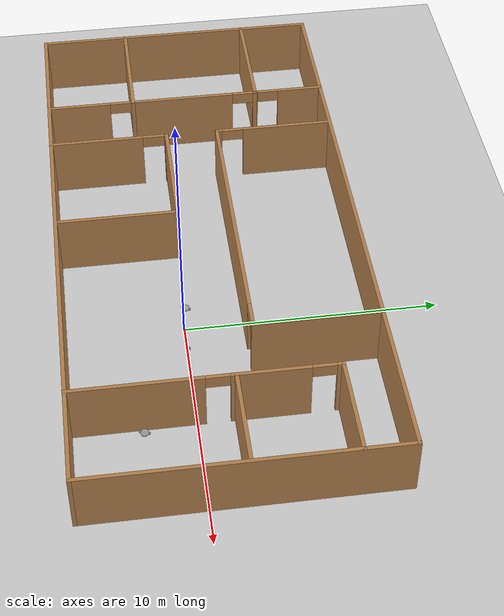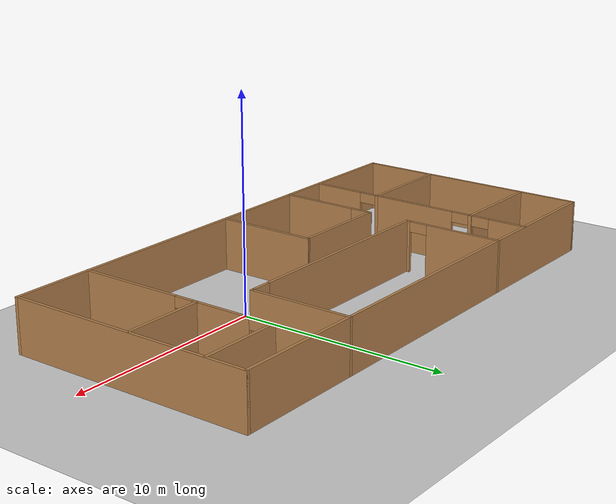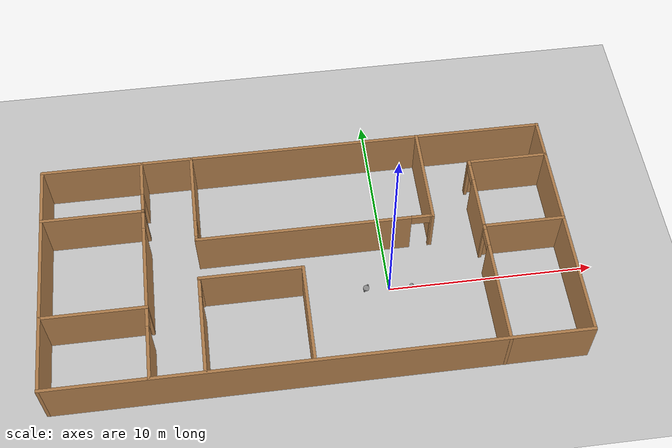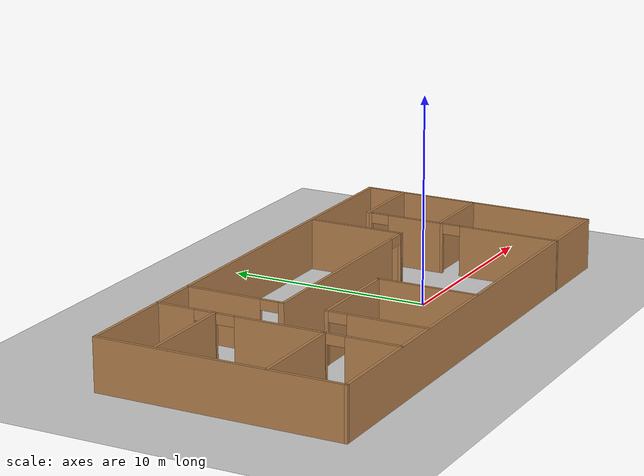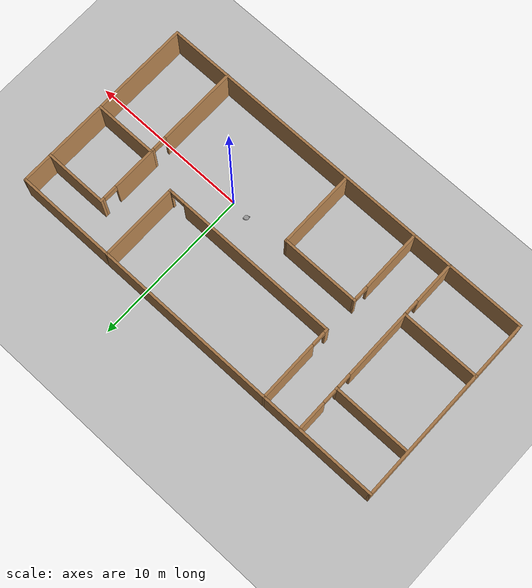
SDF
<sdf version="1.6">
 <world name="default">
  <plugin name="hello" filename="libhello.so"/>
  <light name="sun" type="directional">
   <pose>0 0 10 0 -0 0</pose>
   <diffuse>0.8 0.8 0.8 1</diffuse>
   <specular>0.2 0.2 0.2 1</specular>
   <attenuation>
    <range>1000</range>
    <constant>0.9</constant>
    <linear>0.01</linear>
    <quadratic>0.001</quadratic>
   </attenuation>
   <direction>-0.5 0.1 -0.9</direction>
  </light>
  <model name="ground_plane">
   <static>1</static>
   <link name="link">
    <collision name="collision">
     <geometry><plane><normal>0 0 1</normal><size>100 100</size></plane></geometry>
     <surface>
      <contact><collide_bitmask>65535</collide_bitmask></contact>
      <friction><ode><mu>100</mu><mu2>50</mu2></ode></friction>
     </surface>
    </collision>
    <visual name="visual">
     <cast_shadows>0</cast_shadows>
     <geometry><plane><normal>0 0 1</normal><size>100 100</size></plane></geometry>
     <material>
      <script><uri>file://media/materials/scripts/gazebo.material</uri><name>Gazebo/Grey</name></script>
     </material>
    </visual>
   </link>
  </model>
  <gravity>0 0 -9.8</gravity>
  <magnetic_field>6e-06 2.3e-05 -4.2e-05</magnetic_field>
  <atmosphere type="adiabatic"/>
  <physics name="default_physics" default="0" type="ode">
   <max_step_size>0.001</max_step_size>
   <real_time_factor>1</real_time_factor>
   <real_time_update_rate>1000</real_time_update_rate>
  </physics>
  <scene><ambient>0.4 0.4 0.4 1</ambient><background>0.7 0.7 0.7 1</background><shadows>1</shadows></scene>
  <spherical_coordinates>
   <surface_model>EARTH_WGS84</surface_model>
   <latitude_deg>0</latitude_deg>
   <longitude_deg>0</longitude_deg>
   <elevation>0</elevation>
   <heading_deg>0</heading_deg>
  </spherical_coordinates>
  <model name="CleaningRobot">
   <link name="link_0">
    <pose>-0.003333 3e-06 4e-06 0 -0 0</pose>
    <inertial>
     <mass>1</mass>
     <inertia><ixx>0.145833</ixx><ixy>0</ixy><ixz>0</ixz><iyy>0.145833</iyy><iyz>0</iyz><izz>0.125</izz></inertia>
    </inertial>
    <visual name="visual">
     <geometry><cylinder><radius>0.15</radius><length>0.05</length></cylinder></geometry>
     <material>
      <lighting>1</lighting>
      <script><uri>file://media/materials/scripts/gazebo.material</uri><name>Gazebo/Grey</name></script>
      <shader type="pixel"><normal_map>__default__</normal_map></shader>
      <ambient>0.3 0.3 0.3 1</ambient>
      <diffuse>0.7 0.7 0.7 1</diffuse>
      <specular>0.01 0.01 0.01 1</specular>
      <emissive>0 0 0 1</emissive>
     </material>
    </visual>
    <collision name="collision">
     <geometry><cylinder><radius>0.15</radius><length>0.05</length></cylinder></geometry>
     <surface>
      <friction>
       <ode><mu>1</mu><mu2>1</mu2><fdir1>0 0 0</fdir1><slip1>0</slip1><slip2>0</slip2></ode>
       <torsional>
        <coefficient>1</coefficient>
        <patch_radius>0</patch_radius>
        <surface_radius>0</surface_radius>
        <use_patch_radius>1</use_patch_radius>
        <ode><slip>0</slip></ode>
       </torsional>
      </friction>
      <bounce><restitution_coefficient>0</restitution_coefficient><threshold>1e+06</threshold></bounce>
      <contact>
       <collide_without_contact>0</collide_without_contact>
       <collide_without_contact_bitmask>1</collide_without_contact_bitmask>
       <collide_bitmask>1</collide_bitmask>
       <ode>
        <soft_cfm>0</soft_cfm>
        <soft_erp>0.2</soft_erp>
        <kp>1e+13</kp>
        <kd>1</kd>
        <max_vel>0.01</max_vel>
        <min_depth>0</min_depth>
       </ode>
       <bullet>
        <split_impulse>1</split_impulse>
        <split_impulse_penetration_threshold>-0.01</split_impulse_penetration_threshold>
        <soft_cfm>0</soft_cfm>
        <soft_erp>0.2</soft_erp>
        <kp>1e+13</kp>
        <kd>1</kd>
       </bullet>
      </contact>
     </surface>
    </collision>
   </link>
   <link name="link_1">
    <pose>0.006667 -0.175011 -1e-05 1.5707 -0 0</pose>
    <inertial>
     <mass>1</mass>
     <inertia><ixx>0.145833</ixx><ixy>0</ixy><ixz>0</ixz><iyy>0.145833</iyy><iyz>0</iyz><izz>0.125</izz></inertia>
    </inertial>
    <visual name="visual">
     <geometry><cylinder><radius>0.05</radius><length>0.05</length></cylinder></geometry>
     <material>
      <lighting>1</lighting>
      <script><uri>file://media/materials/scripts/gazebo.material</uri><name>Gazebo/Grey</name></script>
      <shader type="pixel"><normal_map>__default__</normal_map></shader>
      <ambient>0.3 0.3 0.3 1</ambient>
      <diffuse>0.7 0.7 0.7 1</diffuse>
      <specular>0.01 0.01 0.01 1</specular>
      <emissive>0 0 0 1</emissive>
     </material>
    </visual>
    <collision name="collision">
     <geometry><cylinder><radius>0.05</radius><length>0.05</length></cylinder></geometry>
     <surface>
      <friction>
       <ode><mu>1</mu><mu2>1</mu2><fdir1>0 0 0</fdir1><slip1>0</slip1><slip2>0</slip2></ode>
       <torsional>
        <coefficient>1</coefficient>
        <patch_radius>0</patch_radius>
        <surface_radius>0</surface_radius>
        <use_patch_radius>1</use_patch_radius>
        <ode><slip>0</slip></ode>
       </torsional>
      </friction>
      <bounce><restitution_coefficient>0</restitution_coefficient><threshold>1e+06</threshold></bounce>
      <contact>
       <collide_without_contact>0</collide_without_contact>
       <collide_without_contact_bitmask>1</collide_without_contact_bitmask>
       <collide_bitmask>1</collide_bitmask>
       <ode>
        <soft_cfm>0</soft_cfm>
        <soft_erp>0.2</soft_erp>
        <kp>1e+13</kp>
        <kd>1</kd>
        <max_vel>0.01</max_vel>
        <min_depth>0</min_depth>
       </ode>
       <bullet>
        <split_impulse>1</split_impulse>
        <split_impulse_penetration_threshold>-0.01</split_impulse_penetration_threshold>
        <soft_cfm>0</soft_cfm>
        <soft_erp>0.2</soft_erp>
        <kp>1e+13</kp>
        <kd>1</kd>
       </bullet>
      </contact>
     </surface>
    </collision>
   </link>
   <link name="link_1_clone">
    <pose>-0.003333 0.175008 6e-06 1.5707 -0 0</pose>
    <inertial>
     <mass>1</mass>
     <inertia><ixx>0.145833</ixx><ixy>0</ixy><ixz>0</ixz><iyy>0.145833</iyy><iyz>0</iyz><izz>0.125</izz></inertia>
    </inertial>
    <visual name="visual">
     <geometry><cylinder><radius>0.05</radius><length>0.05</length></cylinder></geometry>
     <material>
      <lighting>1</lighting>
      <script><uri>file://media/materials/scripts/gazebo.material</uri><name>Gazebo/Grey</name></script>
      <shader type="pixel"><normal_map>__default__</normal_map></shader>
      <ambient>0.3 0.3 0.3 1</ambient>
      <diffuse>0.7 0.7 0.7 1</diffuse>
      <specular>0.01 0.01 0.01 1</specular>
      <emissive>0 0 0 1</emissive>
     </material>
    </visual>
    <collision name="collision">
     <geometry><cylinder><radius>0.05</radius><length>0.05</length></cylinder></geometry>
     <surface>
      <friction>
       <ode><mu>1</mu><mu2>1</mu2><fdir1>0 0 0</fdir1><slip1>0</slip1><slip2>0</slip2></ode>
       <torsional>
        <coefficient>1</coefficient>
        <patch_radius>0</patch_radius>
        <surface_radius>0</surface_radius>
        <use_patch_radius>1</use_patch_radius>
        <ode><slip>0</slip></ode>
       </torsional>
      </friction>
      <bounce><restitution_coefficient>0</restitution_coefficient><threshold>1e+06</threshold></bounce>
      <contact>
       <collide_without_contact>0</collide_without_contact>
       <collide_without_contact_bitmask>1</collide_without_contact_bitmask>
       <collide_bitmask>1</collide_bitmask>
       <ode>
        <soft_cfm>0</soft_cfm>
        <soft_erp>0.2</soft_erp>
        <kp>1e+13</kp>
        <kd>1</kd>
        <max_vel>0.01</max_vel>
        <min_depth>0</min_depth>
       </ode>
       <bullet>
        <split_impulse>1</split_impulse>
        <split_impulse_penetration_threshold>-0.01</split_impulse_penetration_threshold>
        <soft_cfm>0</soft_cfm>
        <soft_erp>0.2</soft_erp>
        <kp>1e+13</kp>
        <kd>1</kd>
       </bullet>
      </contact>
     </surface>
    </collision>
   </link>
   <joint name="link_0_JOINT_0" type="revolute">
    <parent>link_0</parent>
    <child>link_1</child>
    <axis>
     <xyz>0 0 1</xyz>
     <use_parent_model_frame>0</use_parent_model_frame>
     <limit>
      <lower>-1.79769e+308</lower>
      <upper>1.79769e+308</upper>
      <effort>-1</effort>
      <velocity>-1</velocity>
     </limit>
     <dynamics>
      <spring_reference>0</spring_reference>
      <spring_stiffness>0</spring_stiffness>
      <damping>0</damping>
     </dynamics>
    </axis>
    <physics>
     <ode><limit><cfm>0</cfm><erp>0.2</erp></limit><suspension><cfm>0</cfm><erp>0.2</erp></suspension></ode>
    </physics>
   </joint>
   <joint name="link_0_JOINT_1" type="revolute">
    <parent>link_0</parent>
    <child>link_1_clone</child>
    <axis>
     <xyz>0 0 1</xyz>
     <use_parent_model_frame>0</use_parent_model_frame>
     <limit>
      <lower>-1.79769e+308</lower>
      <upper>1.79769e+308</upper>
      <effort>-1</effort>
      <velocity>-1</velocity>
     </limit>
     <dynamics>
      <spring_reference>0</spring_reference>
      <spring_stiffness>0</spring_stiffness>
      <damping>0</damping>
     </dynamics>
    </axis>
    <physics>
     <ode><limit><cfm>0</cfm><erp>0.2</erp></limit><suspension><cfm>0</cfm><erp>0.2</erp></suspension></ode>
    </physics>
   </joint>
   <static>0</static>
   <pose>4.93871 -1.93224 0.049842 0.004706 -0.164816 2.77664</pose>
  </model>
  <model name="Building">
   <link name="Wall_19">
    <pose>0 5.9295 0 0 -0 0</pose>
    <visual name="Wall_19_Visual">
     <pose>0 0 1.25 0 -0 0</pose>
     <geometry><box><size>25 0.15 2.5</size></box></geometry>
     <material>
      <script><uri>file://media/materials/scripts/gazebo.material</uri><name>Gazebo/Wood</name></script>
      <ambient>1 1 1 1</ambient>
      <shader type="pixel"/>
      <diffuse>1 1 1 1</diffuse>
      <specular>0.2 0.2 0.2 1</specular>
      <emissive>0 0 0 1</emissive>
     </material>
     <meta><layer>0</layer></meta>
    </visual>
    <collision name="Wall_19_Collision">
     <pose>0 0 1.25 0 -0 0</pose>
     <geometry><box><size>25 0.15 2.5</size></box></geometry>
     <surface>
      <friction>
       <ode><mu>1</mu><mu2>1</mu2><fdir1>0 0 0</fdir1><slip1>0</slip1><slip2>0</slip2></ode>
       <torsional>
        <coefficient>1</coefficient>
        <patch_radius>0</patch_radius>
        <surface_radius>0</surface_radius>
        <use_patch_radius>1</use_patch_radius>
        <ode><slip>0</slip></ode>
       </torsional>
      </friction>
      <bounce><restitution_coefficient>0</restitution_coefficient><threshold>1e+06</threshold></bounce>
      <contact>
       <collide_without_contact>0</collide_without_contact>
       <collide_without_contact_bitmask>1</collide_without_contact_bitmask>
       <collide_bitmask>1</collide_bitmask>
       <ode>
        <soft_cfm>0</soft_cfm>
        <soft_erp>0.2</soft_erp>
        <kp>1e+13</kp>
        <kd>1</kd>
        <max_vel>0.01</max_vel>
        <min_depth>0</min_depth>
       </ode>
       <bullet>
        <split_impulse>1</split_impulse>
        <split_impulse_penetration_threshold>-0.01</split_impulse_penetration_threshold>
        <soft_cfm>0</soft_cfm>
        <soft_erp>0.2</soft_erp>
        <kp>1e+13</kp>
        <kd>1</kd>
       </bullet>
      </contact>
     </surface>
    </collision>
   </link>
   <link name="Wall_20">
    <pose>12.425 0.0045 0 0 0 -1.5708</pose>
    <visual name="Wall_20_Visual">
     <pose>0 0 1.25 0 -0 0</pose>
     <geometry><box><size>12 0.15 2.5</size></box></geometry>
     <material>
      <script><uri>file://media/materials/scripts/gazebo.material</uri><name>Gazebo/Wood</name></script>
      <ambient>1 1 1 1</ambient>
      <shader type="pixel"/>
      <diffuse>1 1 1 1</diffuse>
      <specular>0.2 0.2 0.2 1</specular>
      <emissive>0 0 0 1</emissive>
     </material>
     <meta><layer>0</layer></meta>
    </visual>
    <collision name="Wall_20_Collision">
     <pose>0 0 1.25 0 -0 0</pose>
     <geometry><box><size>12 0.15 2.5</size></box></geometry>
     <surface>
      <friction>
       <ode><mu>1</mu><mu2>1</mu2><fdir1>0 0 0</fdir1><slip1>0</slip1><slip2>0</slip2></ode>
       <torsional>
        <coefficient>1</coefficient>
        <patch_radius>0</patch_radius>
        <surface_radius>0</surface_radius>
        <use_patch_radius>1</use_patch_radius>
        <ode><slip>0</slip></ode>
       </torsional>
      </friction>
      <bounce><restitution_coefficient>0</restitution_coefficient><threshold>1e+06</threshold></bounce>
      <contact>
       <collide_without_contact>0</collide_without_contact>
       <collide_without_contact_bitmask>1</collide_without_contact_bitmask>
       <collide_bitmask>1</collide_bitmask>
       <ode>
        <soft_cfm>0</soft_cfm>
        <soft_erp>0.2</soft_erp>
        <kp>1e+13</kp>
        <kd>1</kd>
        <max_vel>0.01</max_vel>
        <min_depth>0</min_depth>
       </ode>
       <bullet>
        <split_impulse>1</split_impulse>
        <split_impulse_penetration_threshold>-0.01</split_impulse_penetration_threshold>
        <soft_cfm>0</soft_cfm>
        <soft_erp>0.2</soft_erp>
        <kp>1e+13</kp>
        <kd>1</kd>
       </bullet>
      </contact>
     </surface>
    </collision>
   </link>
   <link name="Wall_21">
    <pose>0 -5.9205 0 0 -0 3.14159</pose>
    <visual name="Wall_21_Visual">
     <pose>0 0 1.25 0 -0 0</pose>
     <geometry><box><size>25 0.15 2.5</size></box></geometry>
     <material>
      <script><uri>file://media/materials/scripts/gazebo.material</uri><name>Gazebo/Wood</name></script>
      <ambient>1 1 1 1</ambient>
      <shader type="pixel"/>
      <diffuse>1 1 1 1</diffuse>
      <specular>0.2 0.2 0.2 1</specular>
      <emissive>0 0 0 1</emissive>
     </material>
     <meta><layer>0</layer></meta>
    </visual>
    <collision name="Wall_21_Collision">
     <pose>0 0 1.25 0 -0 0</pose>
     <geometry><box><size>25 0.15 2.5</size></box></geometry>
     <surface>
      <friction>
       <ode><mu>1</mu><mu2>1</mu2><fdir1>0 0 0</fdir1><slip1>0</slip1><slip2>0</slip2></ode>
       <torsional>
        <coefficient>1</coefficient>
        <patch_radius>0</patch_radius>
        <surface_radius>0</surface_radius>
        <use_patch_radius>1</use_patch_radius>
        <ode><slip>0</slip></ode>
       </torsional>
      </friction>
      <bounce><restitution_coefficient>0</restitution_coefficient><threshold>1e+06</threshold></bounce>
      <contact>
       <collide_without_contact>0</collide_without_contact>
       <collide_without_contact_bitmask>1</collide_without_contact_bitmask>
       <collide_bitmask>1</collide_bitmask>
       <ode>
        <soft_cfm>0</soft_cfm>
        <soft_erp>0.2</soft_erp>
        <kp>1e+13</kp>
        <kd>1</kd>
        <max_vel>0.01</max_vel>
        <min_depth>0</min_depth>
       </ode>
       <bullet>
        <split_impulse>1</split_impulse>
        <split_impulse_penetration_threshold>-0.01</split_impulse_penetration_threshold>
        <soft_cfm>0</soft_cfm>
        <soft_erp>0.2</soft_erp>
        <kp>1e+13</kp>
        <kd>1</kd>
       </bullet>
      </contact>
     </surface>
    </collision>
   </link>
   <link name="Wall_22">
    <pose>-12.425 0.0045 0 0 -0 1.5708</pose>
    <visual name="Wall_22_Visual">
     <pose>0 0 1.25 0 -0 0</pose>
     <geometry><box><size>12 0.15 2.5</size></box></geometry>
     <material>
      <script><uri>file://media/materials/scripts/gazebo.material</uri><name>Gazebo/Wood</name></script>
      <ambient>1 1 1 1</ambient>
      <shader type="pixel"/>
      <diffuse>1 1 1 1</diffuse>
      <specular>0.2 0.2 0.2 1</specular>
      <emissive>0 0 0 1</emissive>
     </material>
     <meta><layer>0</layer></meta>
    </visual>
    <collision name="Wall_22_Collision">
     <pose>0 0 1.25 0 -0 0</pose>
     <geometry><box><size>12 0.15 2.5</size></box></geometry>
     <surface>
      <friction>
       <ode><mu>1</mu><mu2>1</mu2><fdir1>0 0 0</fdir1><slip1>0</slip1><slip2>0</slip2></ode>
       <torsional>
        <coefficient>1</coefficient>
        <patch_radius>0</patch_radius>
        <surface_radius>0</surface_radius>
        <use_patch_radius>1</use_patch_radius>
        <ode><slip>0</slip></ode>
       </torsional>
      </friction>
      <bounce><restitution_coefficient>0</restitution_coefficient><threshold>1e+06</threshold></bounce>
      <contact>
       <collide_without_contact>0</collide_without_contact>
       <collide_without_contact_bitmask>1</collide_without_contact_bitmask>
       <collide_bitmask>1</collide_bitmask>
       <ode>
        <soft_cfm>0</soft_cfm>
        <soft_erp>0.2</soft_erp>
        <kp>1e+13</kp>
        <kd>1</kd>
        <max_vel>0.01</max_vel>
        <min_depth>0</min_depth>
       </ode>
       <bullet>
        <split_impulse>1</split_impulse>
        <split_impulse_penetration_threshold>-0.01</split_impulse_penetration_threshold>
        <soft_cfm>0</soft_cfm>
        <soft_erp>0.2</soft_erp>
        <kp>1e+13</kp>
        <kd>1</kd>
       </bullet>
      </contact>
     </surface>
    </collision>
   </link>
   <link name="Wall_32">
    <pose>10.49 4.0205 0 0 -0 3.14159</pose>
    <visual name="Wall_32_Visual">
     <pose>0 0 1.25 0 -0 0</pose>
     <geometry><box><size>4 0.15 2.5</size></box></geometry>
     <material>
      <script><uri>file://media/materials/scripts/gazebo.material</uri><name>Gazebo/Wood</name></script>
      <ambient>1 1 1 1</ambient>
      <shader type="pixel"/>
      <diffuse>1 1 1 1</diffuse>
      <specular>0.2 0.2 0.2 1</specular>
      <emissive>0 0 0 1</emissive>
     </material>
     <meta><layer>0</layer></meta>
    </visual>
    <collision name="Wall_32_Collision">
     <pose>0 0 1.25 0 -0 0</pose>
     <geometry><box><size>4 0.15 2.5</size></box></geometry>
     <surface>
      <friction>
       <ode><mu>1</mu><mu2>1</mu2><fdir1>0 0 0</fdir1><slip1>0</slip1><slip2>0</slip2></ode>
       <torsional>
        <coefficient>1</coefficient>
        <patch_radius>0</patch_radius>
        <surface_radius>0</surface_radius>
        <use_patch_radius>1</use_patch_radius>
        <ode><slip>0</slip></ode>
       </torsional>
      </friction>
      <bounce><restitution_coefficient>0</restitution_coefficient><threshold>1e+06</threshold></bounce>
      <contact>
       <collide_without_contact>0</collide_without_contact>
       <collide_without_contact_bitmask>1</collide_without_contact_bitmask>
       <collide_bitmask>1</collide_bitmask>
       <ode>
        <soft_cfm>0</soft_cfm>
        <soft_erp>0.2</soft_erp>
        <kp>1e+13</kp>
        <kd>1</kd>
        <max_vel>0.01</max_vel>
        <min_depth>0</min_depth>
       </ode>
       <bullet>
        <split_impulse>1</split_impulse>
        <split_impulse_penetration_threshold>-0.01</split_impulse_penetration_threshold>
        <soft_cfm>0</soft_cfm>
        <soft_erp>0.2</soft_erp>
        <kp>1e+13</kp>
        <kd>1</kd>
       </bullet>
      </contact>
     </surface>
    </collision>
   </link>
   <link name="Wall_33">
    <pose>8.565 2.0955 0 0 0 -1.5708</pose>
    <visual name="Wall_33_Visual_2">
     <pose>-1.25392 0 2.25 0 -0 0</pose>
     <geometry><box><size>0.9 0.15 0.5</size></box></geometry>
     <material>
      <script><uri>file://media/materials/scripts/gazebo.material</uri><name>Gazebo/Wood</name></script>
      <ambient>1 1 1 1</ambient>
      <shader type="pixel"/>
      <diffuse>1 1 1 1</diffuse>
      <specular>0.2 0.2 0.2 1</specular>
      <emissive>0 0 0 1</emissive>
     </material>
     <meta><layer>0</layer></meta>
    </visual>
    <visual name="Wall_33_Visual_1">
     <pose>0.59804 0 1.25 0 -0 0</pose>
     <geometry><box><size>2.80392 0.15 2.5</size></box></geometry>
     <material>
      <script><uri>file://media/materials/scripts/gazebo.material</uri><name>Gazebo/Wood</name></script>
      <ambient>1 1 1 1</ambient>
      <shader type="pixel"/>
      <diffuse>1 1 1 1</diffuse>
      <specular>0.2 0.2 0.2 1</specular>
      <emissive>0 0 0 1</emissive>
     </material>
     <meta><layer>0</layer></meta>
    </visual>
    <visual name="Wall_33_Visual_0">
     <pose>-1.85196 0 1.25 0 -0 0</pose>
     <geometry><box><size>0.29608 0.15 2.5</size></box></geometry>
     <material>
      <script><uri>file://media/materials/scripts/gazebo.material</uri><name>Gazebo/Wood</name></script>
      <ambient>1 1 1 1</ambient>
      <shader type="pixel"/>
      <diffuse>1 1 1 1</diffuse>
      <specular>0.2 0.2 0.2 1</specular>
      <emissive>0 0 0 1</emissive>
     </material>
     <meta><layer>0</layer></meta>
    </visual>
    <collision name="Wall_33_Collision_0">
     <pose>-1.85196 0 1.25 0 -0 0</pose>
     <geometry><box><size>0.29608 0.15 2.5</size></box></geometry>
     <surface>
      <friction>
       <ode><mu>1</mu><mu2>1</mu2><fdir1>0 0 0</fdir1><slip1>0</slip1><slip2>0</slip2></ode>
       <torsional>
        <coefficient>1</coefficient>
        <patch_radius>0</patch_radius>
        <surface_radius>0</surface_radius>
        <use_patch_radius>1</use_patch_radius>
        <ode><slip>0</slip></ode>
       </torsional>
      </friction>
      <bounce><restitution_coefficient>0</restitution_coefficient><threshold>1e+06</threshold></bounce>
      <contact>
       <collide_without_contact>0</collide_without_contact>
       <collide_without_contact_bitmask>1</collide_without_contact_bitmask>
       <collide_bitmask>1</collide_bitmask>
       <ode>
        <soft_cfm>0</soft_cfm>
        <soft_erp>0.2</soft_erp>
        <kp>1e+13</kp>
        <kd>1</kd>
        <max_vel>0.01</max_vel>
        <min_depth>0</min_depth>
       </ode>
       <bullet>
        <split_impulse>1</split_impulse>
        <split_impulse_penetration_threshold>-0.01</split_impulse_penetration_threshold>
        <soft_cfm>0</soft_cfm>
        <soft_erp>0.2</soft_erp>
        <kp>1e+13</kp>
        <kd>1</kd>
       </bullet>
      </contact>
     </surface>
    </collision>
    <collision name="Wall_33_Collision_2">
     <pose>-1.25392 0 2.25 0 -0 0</pose>
     <geometry><box><size>0.9 0.15 0.5</size></box></geometry>
     <surface>
      <friction>
       <ode><mu>1</mu><mu2>1</mu2><fdir1>0 0 0</fdir1><slip1>0</slip1><slip2>0</slip2></ode>
       <torsional>
        <coefficient>1</coefficient>
        <patch_radius>0</patch_radius>
        <surface_radius>0</surface_radius>
        <use_patch_radius>1</use_patch_radius>
        <ode><slip>0</slip></ode>
       </torsional>
      </friction>
      <bounce><restitution_coefficient>0</restitution_coefficient><threshold>1e+06</threshold></bounce>
      <contact>
       <collide_without_contact>0</collide_without_contact>
       <collide_without_contact_bitmask>1</collide_without_contact_bitmask>
       <collide_bitmask>1</collide_bitmask>
       <ode>
        <soft_cfm>0</soft_cfm>
        <soft_erp>0.2</soft_erp>
        <kp>1e+13</kp>
        <kd>1</kd>
        <max_vel>0.01</max_vel>
        <min_depth>0</min_depth>
       </ode>
       <bullet>
        <split_impulse>1</split_impulse>
        <split_impulse_penetration_threshold>-0.01</split_impulse_penetration_threshold>
        <soft_cfm>0</soft_cfm>
        <soft_erp>0.2</soft_erp>
        <kp>1e+13</kp>
        <kd>1</kd>
       </bullet>
      </contact>
     </surface>
    </collision>
    <collision name="Wall_33_Collision_1">
     <pose>0.59804 0 1.25 0 -0 0</pose>
     <geometry><box><size>2.80392 0.15 2.5</size></box></geometry>
     <surface>
      <friction>
       <ode><mu>1</mu><mu2>1</mu2><fdir1>0 0 0</fdir1><slip1>0</slip1><slip2>0</slip2></ode>
       <torsional>
        <coefficient>1</coefficient>
        <patch_radius>0</patch_radius>
        <surface_radius>0</surface_radius>
        <use_patch_radius>1</use_patch_radius>
        <ode><slip>0</slip></ode>
       </torsional>
      </friction>
      <bounce><restitution_coefficient>0</restitution_coefficient><threshold>1e+06</threshold></bounce>
      <contact>
       <collide_without_contact>0</collide_without_contact>
       <collide_without_contact_bitmask>1</collide_without_contact_bitmask>
       <collide_bitmask>1</collide_bitmask>
       <ode>
        <soft_cfm>0</soft_cfm>
        <soft_erp>0.2</soft_erp>
        <kp>1e+13</kp>
        <kd>1</kd>
        <max_vel>0.01</max_vel>
        <min_depth>0</min_depth>
       </ode>
       <bullet>
        <split_impulse>1</split_impulse>
        <split_impulse_penetration_threshold>-0.01</split_impulse_penetration_threshold>
        <soft_cfm>0</soft_cfm>
        <soft_erp>0.2</soft_erp>
        <kp>1e+13</kp>
        <kd>1</kd>
       </bullet>
      </contact>
     </surface>
    </collision>
   </link>
   <link name="Wall_34">
    <pose>10.49 0.1705 0 0 -0 0</pose>
    <visual name="Wall_34_Visual">
     <pose>0 0 1.25 0 -0 0</pose>
     <geometry><box><size>4 0.15 2.5</size></box></geometry>
     <material>
      <script><uri>file://media/materials/scripts/gazebo.material</uri><name>Gazebo/Wood</name></script>
      <ambient>1 1 1 1</ambient>
      <shader type="pixel"/>
      <diffuse>1 1 1 1</diffuse>
      <specular>0.2 0.2 0.2 1</specular>
      <emissive>0 0 0 1</emissive>
     </material>
     <meta><layer>0</layer></meta>
    </visual>
    <collision name="Wall_34_Collision">
     <pose>0 0 1.25 0 -0 0</pose>
     <geometry><box><size>4 0.15 2.5</size></box></geometry>
     <surface>
      <friction>
       <ode><mu>1</mu><mu2>1</mu2><fdir1>0 0 0</fdir1><slip1>0</slip1><slip2>0</slip2></ode>
       <torsional>
        <coefficient>1</coefficient>
        <patch_radius>0</patch_radius>
        <surface_radius>0</surface_radius>
        <use_patch_radius>1</use_patch_radius>
        <ode><slip>0</slip></ode>
       </torsional>
      </friction>
      <bounce><restitution_coefficient>0</restitution_coefficient><threshold>1e+06</threshold></bounce>
      <contact>
       <collide_without_contact>0</collide_without_contact>
       <collide_without_contact_bitmask>1</collide_without_contact_bitmask>
       <collide_bitmask>1</collide_bitmask>
       <ode>
        <soft_cfm>0</soft_cfm>
        <soft_erp>0.2</soft_erp>
        <kp>1e+13</kp>
        <kd>1</kd>
        <max_vel>0.01</max_vel>
        <min_depth>0</min_depth>
       </ode>
       <bullet>
        <split_impulse>1</split_impulse>
        <split_impulse_penetration_threshold>-0.01</split_impulse_penetration_threshold>
        <soft_cfm>0</soft_cfm>
        <soft_erp>0.2</soft_erp>
        <kp>1e+13</kp>
        <kd>1</kd>
       </bullet>
      </contact>
     </surface>
    </collision>
   </link>
   <link name="Wall_38">
    <pose>8.565 -2.8795 0 0 0 -1.5708</pose>
    <visual name="Wall_38_Visual_0">
     <pose>-2.97805 0 1.25 0 -0 0</pose>
     <geometry><box><size>0.293894 0.15 2.5</size></box></geometry>
     <material>
      <script><uri>file://media/materials/scripts/gazebo.material</uri><name>Gazebo/Wood</name></script>
      <ambient>1 1 1 1</ambient>
      <shader type="pixel"/>
      <diffuse>1 1 1 1</diffuse>
      <specular>0.2 0.2 0.2 1</specular>
      <emissive>0 0 0 1</emissive>
     </material>
     <meta><layer>0</layer></meta>
    </visual>
    <visual name="Wall_38_Visual_2">
     <pose>-2.38111 0 2.25 0 -0 0</pose>
     <geometry><box><size>0.9 0.15 0.5</size></box></geometry>
     <material>
      <script><uri>file://media/materials/scripts/gazebo.material</uri><name>Gazebo/Wood</name></script>
      <ambient>1 1 1 1</ambient>
      <shader type="pixel"/>
      <diffuse>1 1 1 1</diffuse>
      <specular>0.2 0.2 0.2 1</specular>
      <emissive>0 0 0 1</emissive>
     </material>
     <meta><layer>0</layer></meta>
    </visual>
    <visual name="Wall_38_Visual_1">
     <pose>0.596947 0 1.25 0 -0 0</pose>
     <geometry><box><size>5.05611 0.15 2.5</size></box></geometry>
     <material>
      <script><uri>file://media/materials/scripts/gazebo.material</uri><name>Gazebo/Wood</name></script>
      <ambient>1 1 1 1</ambient>
      <shader type="pixel"/>
      <diffuse>1 1 1 1</diffuse>
      <specular>0.2 0.2 0.2 1</specular>
      <emissive>0 0 0 1</emissive>
     </material>
     <meta><layer>0</layer></meta>
    </visual>
    <collision name="Wall_38_Collision_1">
     <pose>0.596947 0 1.25 0 -0 0</pose>
     <geometry><box><size>5.05611 0.15 2.5</size></box></geometry>
     <surface>
      <friction>
       <ode><mu>1</mu><mu2>1</mu2><fdir1>0 0 0</fdir1><slip1>0</slip1><slip2>0</slip2></ode>
       <torsional>
        <coefficient>1</coefficient>
        <patch_radius>0</patch_radius>
        <surface_radius>0</surface_radius>
        <use_patch_radius>1</use_patch_radius>
        <ode><slip>0</slip></ode>
       </torsional>
      </friction>
      <bounce><restitution_coefficient>0</restitution_coefficient><threshold>1e+06</threshold></bounce>
      <contact>
       <collide_without_contact>0</collide_without_contact>
       <collide_without_contact_bitmask>1</collide_without_contact_bitmask>
       <collide_bitmask>1</collide_bitmask>
       <ode>
        <soft_cfm>0</soft_cfm>
        <soft_erp>0.2</soft_erp>
        <kp>1e+13</kp>
        <kd>1</kd>
        <max_vel>0.01</max_vel>
        <min_depth>0</min_depth>
       </ode>
       <bullet>
        <split_impulse>1</split_impulse>
        <split_impulse_penetration_threshold>-0.01</split_impulse_penetration_threshold>
        <soft_cfm>0</soft_cfm>
        <soft_erp>0.2</soft_erp>
        <kp>1e+13</kp>
        <kd>1</kd>
       </bullet>
      </contact>
     </surface>
    </collision>
    <collision name="Wall_38_Collision_2">
     <pose>-2.38111 0 2.25 0 -0 0</pose>
     <geometry><box><size>0.9 0.15 0.5</size></box></geometry>
     <surface>
      <friction>
       <ode><mu>1</mu><mu2>1</mu2><fdir1>0 0 0</fdir1><slip1>0</slip1><slip2>0</slip2></ode>
       <torsional>
        <coefficient>1</coefficient>
        <patch_radius>0</patch_radius>
        <surface_radius>0</surface_radius>
        <use_patch_radius>1</use_patch_radius>
        <ode><slip>0</slip></ode>
       </torsional>
      </friction>
      <bounce><restitution_coefficient>0</restitution_coefficient><threshold>1e+06</threshold></bounce>
      <contact>
       <collide_without_contact>0</collide_without_contact>
       <collide_without_contact_bitmask>1</collide_without_contact_bitmask>
       <collide_bitmask>1</collide_bitmask>
       <ode>
        <soft_cfm>0</soft_cfm>
        <soft_erp>0.2</soft_erp>
        <kp>1e+13</kp>
        <kd>1</kd>
        <max_vel>0.01</max_vel>
        <min_depth>0</min_depth>
       </ode>
       <bullet>
        <split_impulse>1</split_impulse>
        <split_impulse_penetration_threshold>-0.01</split_impulse_penetration_threshold>
        <soft_cfm>0</soft_cfm>
        <soft_erp>0.2</soft_erp>
        <kp>1e+13</kp>
        <kd>1</kd>
       </bullet>
      </contact>
     </surface>
    </collision>
    <collision name="Wall_38_Collision_0">
     <pose>-2.97805 0 1.25 0 -0 0</pose>
     <geometry><box><size>0.293894 0.15 2.5</size></box></geometry>
     <surface>
      <friction>
       <ode><mu>1</mu><mu2>1</mu2><fdir1>0 0 0</fdir1><slip1>0</slip1><slip2>0</slip2></ode>
       <torsional>
        <coefficient>1</coefficient>
        <patch_radius>0</patch_radius>
        <surface_radius>0</surface_radius>
        <use_patch_radius>1</use_patch_radius>
        <ode><slip>0</slip></ode>
       </torsional>
      </friction>
      <bounce><restitution_coefficient>0</restitution_coefficient><threshold>1e+06</threshold></bounce>
      <contact>
       <collide_without_contact>0</collide_without_contact>
       <collide_without_contact_bitmask>1</collide_without_contact_bitmask>
       <collide_bitmask>1</collide_bitmask>
       <ode>
        <soft_cfm>0</soft_cfm>
        <soft_erp>0.2</soft_erp>
        <kp>1e+13</kp>
        <kd>1</kd>
        <max_vel>0.01</max_vel>
        <min_depth>0</min_depth>
       </ode>
       <bullet>
        <split_impulse>1</split_impulse>
        <split_impulse_penetration_threshold>-0.01</split_impulse_penetration_threshold>
        <soft_cfm>0</soft_cfm>
        <soft_erp>0.2</soft_erp>
        <kp>1e+13</kp>
        <kd>1</kd>
       </bullet>
      </contact>
     </surface>
    </collision>
   </link>
   <link name="Wall_46">
    <pose>-9.99667 3.05607 0 0 -0 3.14159</pose>
    <visual name="Wall_46_Visual">
     <pose>0 0 1.25 0 -0 0</pose>
     <geometry><box><size>5 0.15 2.5</size></box></geometry>
     <material>
      <script><uri>file://media/materials/scripts/gazebo.material</uri><name>Gazebo/Wood</name></script>
      <ambient>1 1 1 1</ambient>
      <shader type="pixel"/>
      <diffuse>1 1 1 1</diffuse>
      <specular>0.2 0.2 0.2 1</specular>
      <emissive>0 0 0 1</emissive>
     </material>
     <meta><layer>0</layer></meta>
    </visual>
    <collision name="Wall_46_Collision">
     <pose>0 0 1.25 0 -0 0</pose>
     <geometry><box><size>5 0.15 2.5</size></box></geometry>
     <surface>
      <friction>
       <ode><mu>1</mu><mu2>1</mu2><fdir1>0 0 0</fdir1><slip1>0</slip1><slip2>0</slip2></ode>
       <torsional>
        <coefficient>1</coefficient>
        <patch_radius>0</patch_radius>
        <surface_radius>0</surface_radius>
        <use_patch_radius>1</use_patch_radius>
        <ode><slip>0</slip></ode>
       </torsional>
      </friction>
      <bounce><restitution_coefficient>0</restitution_coefficient><threshold>1e+06</threshold></bounce>
      <contact>
       <collide_without_contact>0</collide_without_contact>
       <collide_without_contact_bitmask>1</collide_without_contact_bitmask>
       <collide_bitmask>1</collide_bitmask>
       <ode>
        <soft_cfm>0</soft_cfm>
        <soft_erp>0.2</soft_erp>
        <kp>1e+13</kp>
        <kd>1</kd>
        <max_vel>0.01</max_vel>
        <min_depth>0</min_depth>
       </ode>
       <bullet>
        <split_impulse>1</split_impulse>
        <split_impulse_penetration_threshold>-0.01</split_impulse_penetration_threshold>
        <soft_cfm>0</soft_cfm>
        <soft_erp>0.2</soft_erp>
        <kp>1e+13</kp>
        <kd>1</kd>
       </bullet>
      </contact>
     </surface>
    </collision>
   </link>
   <link name="Wall_48">
    <pose>-7.57167 4.48107 0 0 -0 1.5708</pose>
    <visual name="Wall_48_Visual_2">
     <pose>-0.874567 0 2.25 0 -0 0</pose>
     <geometry><box><size>0.9 0.15 0.5</size></box></geometry>
     <material>
      <script><uri>file://media/materials/scripts/gazebo.material</uri><name>Gazebo/Wood</name></script>
      <ambient>1 1 1 1</ambient>
      <shader type="pixel"/>
      <diffuse>1 1 1 1</diffuse>
      <specular>0.2 0.2 0.2 1</specular>
      <emissive>0 0 0 1</emissive>
     </material>
     <meta><layer>0</layer></meta>
    </visual>
    <visual name="Wall_48_Visual_1">
     <pose>0.537716 0 1.25 0 -0 0</pose>
     <geometry><box><size>1.92457 0.15 2.5</size></box></geometry>
     <material>
      <script><uri>file://media/materials/scripts/gazebo.material</uri><name>Gazebo/Wood</name></script>
      <ambient>1 1 1 1</ambient>
      <shader type="pixel"/>
      <diffuse>1 1 1 1</diffuse>
      <specular>0.2 0.2 0.2 1</specular>
      <emissive>0 0 0 1</emissive>
     </material>
     <meta><layer>0</layer></meta>
    </visual>
    <visual name="Wall_48_Visual_0">
     <pose>-1.41228 0 1.25 0 -0 0</pose>
     <geometry><box><size>0.175433 0.15 2.5</size></box></geometry>
     <material>
      <script><uri>file://media/materials/scripts/gazebo.material</uri><name>Gazebo/Wood</name></script>
      <ambient>1 1 1 1</ambient>
      <shader type="pixel"/>
      <diffuse>1 1 1 1</diffuse>
      <specular>0.2 0.2 0.2 1</specular>
      <emissive>0 0 0 1</emissive>
     </material>
     <meta><layer>0</layer></meta>
    </visual>
    <collision name="Wall_48_Collision_2">
     <pose>-0.874567 0 2.25 0 -0 0</pose>
     <geometry><box><size>0.9 0.15 0.5</size></box></geometry>
     <surface>
      <friction>
       <ode><mu>1</mu><mu2>1</mu2><fdir1>0 0 0</fdir1><slip1>0</slip1><slip2>0</slip2></ode>
       <torsional>
        <coefficient>1</coefficient>
        <patch_radius>0</patch_radius>
        <surface_radius>0</surface_radius>
        <use_patch_radius>1</use_patch_radius>
        <ode><slip>0</slip></ode>
       </torsional>
      </friction>
      <bounce><restitution_coefficient>0</restitution_coefficient><threshold>1e+06</threshold></bounce>
      <contact>
       <collide_without_contact>0</collide_without_contact>
       <collide_without_contact_bitmask>1</collide_without_contact_bitmask>
       <collide_bitmask>1</collide_bitmask>
       <ode>
        <soft_cfm>0</soft_cfm>
        <soft_erp>0.2</soft_erp>
        <kp>1e+13</kp>
        <kd>1</kd>
        <max_vel>0.01</max_vel>
        <min_depth>0</min_depth>
       </ode>
       <bullet>
        <split_impulse>1</split_impulse>
        <split_impulse_penetration_threshold>-0.01</split_impulse_penetration_threshold>
        <soft_cfm>0</soft_cfm>
        <soft_erp>0.2</soft_erp>
        <kp>1e+13</kp>
        <kd>1</kd>
       </bullet>
      </contact>
     </surface>
    </collision>
    <collision name="Wall_48_Collision_1">
     <pose>0.537716 0 1.25 0 -0 0</pose>
     <geometry><box><size>1.92457 0.15 2.5</size></box></geometry>
     <surface>
      <friction>
       <ode><mu>1</mu><mu2>1</mu2><fdir1>0 0 0</fdir1><slip1>0</slip1><slip2>0</slip2></ode>
       <torsional>
        <coefficient>1</coefficient>
        <patch_radius>0</patch_radius>
        <surface_radius>0</surface_radius>
        <use_patch_radius>1</use_patch_radius>
        <ode><slip>0</slip></ode>
       </torsional>
      </friction>
      <bounce><restitution_coefficient>0</restitution_coefficient><threshold>1e+06</threshold></bounce>
      <contact>
       <collide_without_contact>0</collide_without_contact>
       <collide_without_contact_bitmask>1</collide_without_contact_bitmask>
       <collide_bitmask>1</collide_bitmask>
       <ode>
        <soft_cfm>0</soft_cfm>
        <soft_erp>0.2</soft_erp>
        <kp>1e+13</kp>
        <kd>1</kd>
        <max_vel>0.01</max_vel>
        <min_depth>0</min_depth>
       </ode>
       <bullet>
        <split_impulse>1</split_impulse>
        <split_impulse_penetration_threshold>-0.01</split_impulse_penetration_threshold>
        <soft_cfm>0</soft_cfm>
        <soft_erp>0.2</soft_erp>
        <kp>1e+13</kp>
        <kd>1</kd>
       </bullet>
      </contact>
     </surface>
    </collision>
    <collision name="Wall_48_Collision_0">
     <pose>-1.41228 0 1.25 0 -0 0</pose>
     <geometry><box><size>0.175433 0.15 2.5</size></box></geometry>
     <surface>
      <friction>
       <ode><mu>1</mu><mu2>1</mu2><fdir1>0 0 0</fdir1><slip1>0</slip1><slip2>0</slip2></ode>
       <torsional>
        <coefficient>1</coefficient>
        <patch_radius>0</patch_radius>
        <surface_radius>0</surface_radius>
        <use_patch_radius>1</use_patch_radius>
        <ode><slip>0</slip></ode>
       </torsional>
      </friction>
      <bounce><restitution_coefficient>0</restitution_coefficient><threshold>1e+06</threshold></bounce>
      <contact>
       <collide_without_contact>0</collide_without_contact>
       <collide_without_contact_bitmask>1</collide_without_contact_bitmask>
       <collide_bitmask>1</collide_bitmask>
       <ode>
        <soft_cfm>0</soft_cfm>
        <soft_erp>0.2</soft_erp>
        <kp>1e+13</kp>
        <kd>1</kd>
        <max_vel>0.01</max_vel>
        <min_depth>0</min_depth>
       </ode>
       <bullet>
        <split_impulse>1</split_impulse>
        <split_impulse_penetration_threshold>-0.01</split_impulse_penetration_threshold>
        <soft_cfm>0</soft_cfm>
        <soft_erp>0.2</soft_erp>
        <kp>1e+13</kp>
        <kd>1</kd>
       </bullet>
      </contact>
     </surface>
    </collision>
   </link>
   <link name="Wall_50">
    <pose>-9.99667 -2.29393 0 0 -0 0</pose>
    <visual name="Wall_50_Visual">
     <pose>0 0 1.25 0 -0 0</pose>
     <geometry><box><size>5 0.15 2.5</size></box></geometry>
     <material>
      <script><uri>file://media/materials/scripts/gazebo.material</uri><name>Gazebo/Wood</name></script>
      <ambient>1 1 1 1</ambient>
      <shader type="pixel"/>
      <diffuse>1 1 1 1</diffuse>
      <specular>0.2 0.2 0.2 1</specular>
      <emissive>0 0 0 1</emissive>
     </material>
     <meta><layer>0</layer></meta>
    </visual>
    <collision name="Wall_50_Collision">
     <pose>0 0 1.25 0 -0 0</pose>
     <geometry><box><size>5 0.15 2.5</size></box></geometry>
     <surface>
      <friction>
       <ode><mu>1</mu><mu2>1</mu2><fdir1>0 0 0</fdir1><slip1>0</slip1><slip2>0</slip2></ode>
       <torsional>
        <coefficient>1</coefficient>
        <patch_radius>0</patch_radius>
        <surface_radius>0</surface_radius>
        <use_patch_radius>1</use_patch_radius>
        <ode><slip>0</slip></ode>
       </torsional>
      </friction>
      <bounce><restitution_coefficient>0</restitution_coefficient><threshold>1e+06</threshold></bounce>
      <contact>
       <collide_without_contact>0</collide_without_contact>
       <collide_without_contact_bitmask>1</collide_without_contact_bitmask>
       <collide_bitmask>1</collide_bitmask>
       <ode>
        <soft_cfm>0</soft_cfm>
        <soft_erp>0.2</soft_erp>
        <kp>1e+13</kp>
        <kd>1</kd>
        <max_vel>0.01</max_vel>
        <min_depth>0</min_depth>
       </ode>
       <bullet>
        <split_impulse>1</split_impulse>
        <split_impulse_penetration_threshold>-0.01</split_impulse_penetration_threshold>
        <soft_cfm>0</soft_cfm>
        <soft_erp>0.2</soft_erp>
        <kp>1e+13</kp>
        <kd>1</kd>
       </bullet>
      </contact>
     </surface>
    </collision>
   </link>
   <link name="Wall_51">
    <pose>-7.57167 -4.09393 0 0 0 -1.5708</pose>
    <visual name="Wall_51_Visual_1">
     <pose>0.536564 0 1.25 0 -0 0</pose>
     <geometry><box><size>2.67687 0.15 2.5</size></box></geometry>
     <material>
      <script><uri>file://media/materials/scripts/gazebo.material</uri><name>Gazebo/Wood</name></script>
      <ambient>1 1 1 1</ambient>
      <shader type="pixel"/>
      <diffuse>1 1 1 1</diffuse>
      <specular>0.2 0.2 0.2 1</specular>
      <emissive>0 0 0 1</emissive>
     </material>
     <meta><layer>0</layer></meta>
    </visual>
    <visual name="Wall_51_Visual_0">
     <pose>-1.78844 0 1.25 0 -0 0</pose>
     <geometry><box><size>0.173129 0.15 2.5</size></box></geometry>
     <material>
      <script><uri>file://media/materials/scripts/gazebo.material</uri><name>Gazebo/Wood</name></script>
      <ambient>1 1 1 1</ambient>
      <shader type="pixel"/>
      <diffuse>1 1 1 1</diffuse>
      <specular>0.2 0.2 0.2 1</specular>
      <emissive>0 0 0 1</emissive>
     </material>
     <meta><layer>0</layer></meta>
    </visual>
    <visual name="Wall_51_Visual_2">
     <pose>-1.25187 0 2.25 0 -0 0</pose>
     <geometry><box><size>0.9 0.15 0.5</size></box></geometry>
     <material>
      <script><uri>file://media/materials/scripts/gazebo.material</uri><name>Gazebo/Wood</name></script>
      <ambient>1 1 1 1</ambient>
      <shader type="pixel"/>
      <diffuse>1 1 1 1</diffuse>
      <specular>0.2 0.2 0.2 1</specular>
      <emissive>0 0 0 1</emissive>
     </material>
     <meta><layer>0</layer></meta>
    </visual>
    <collision name="Wall_51_Collision_0">
     <pose>-1.78844 0 1.25 0 -0 0</pose>
     <geometry><box><size>0.173129 0.15 2.5</size></box></geometry>
     <surface>
      <friction>
       <ode><mu>1</mu><mu2>1</mu2><fdir1>0 0 0</fdir1><slip1>0</slip1><slip2>0</slip2></ode>
       <torsional>
        <coefficient>1</coefficient>
        <patch_radius>0</patch_radius>
        <surface_radius>0</surface_radius>
        <use_patch_radius>1</use_patch_radius>
        <ode><slip>0</slip></ode>
       </torsional>
      </friction>
      <bounce><restitution_coefficient>0</restitution_coefficient><threshold>1e+06</threshold></bounce>
      <contact>
       <collide_without_contact>0</collide_without_contact>
       <collide_without_contact_bitmask>1</collide_without_contact_bitmask>
       <collide_bitmask>1</collide_bitmask>
       <ode>
        <soft_cfm>0</soft_cfm>
        <soft_erp>0.2</soft_erp>
        <kp>1e+13</kp>
        <kd>1</kd>
        <max_vel>0.01</max_vel>
        <min_depth>0</min_depth>
       </ode>
       <bullet>
        <split_impulse>1</split_impulse>
        <split_impulse_penetration_threshold>-0.01</split_impulse_penetration_threshold>
        <soft_cfm>0</soft_cfm>
        <soft_erp>0.2</soft_erp>
        <kp>1e+13</kp>
        <kd>1</kd>
       </bullet>
      </contact>
     </surface>
    </collision>
    <collision name="Wall_51_Collision_2">
     <pose>-1.25187 0 2.25 0 -0 0</pose>
     <geometry><box><size>0.9 0.15 0.5</size></box></geometry>
     <surface>
      <friction>
       <ode><mu>1</mu><mu2>1</mu2><fdir1>0 0 0</fdir1><slip1>0</slip1><slip2>0</slip2></ode>
       <torsional>
        <coefficient>1</coefficient>
        <patch_radius>0</patch_radius>
        <surface_radius>0</surface_radius>
        <use_patch_radius>1</use_patch_radius>
        <ode><slip>0</slip></ode>
       </torsional>
      </friction>
      <bounce><restitution_coefficient>0</restitution_coefficient><threshold>1e+06</threshold></bounce>
      <contact>
       <collide_without_contact>0</collide_without_contact>
       <collide_without_contact_bitmask>1</collide_without_contact_bitmask>
       <collide_bitmask>1</collide_bitmask>
       <ode>
        <soft_cfm>0</soft_cfm>
        <soft_erp>0.2</soft_erp>
        <kp>1e+13</kp>
        <kd>1</kd>
        <max_vel>0.01</max_vel>
        <min_depth>0</min_depth>
       </ode>
       <bullet>
        <split_impulse>1</split_impulse>
        <split_impulse_penetration_threshold>-0.01</split_impulse_penetration_threshold>
        <soft_cfm>0</soft_cfm>
        <soft_erp>0.2</soft_erp>
        <kp>1e+13</kp>
        <kd>1</kd>
       </bullet>
      </contact>
     </surface>
    </collision>
    <collision name="Wall_51_Collision_1">
     <pose>0.536564 0 1.25 0 -0 0</pose>
     <geometry><box><size>2.67687 0.15 2.5</size></box></geometry>
     <surface>
      <friction>
       <ode><mu>1</mu><mu2>1</mu2><fdir1>0 0 0</fdir1><slip1>0</slip1><slip2>0</slip2></ode>
       <torsional>
        <coefficient>1</coefficient>
        <patch_radius>0</patch_radius>
        <surface_radius>0</surface_radius>
        <use_patch_radius>1</use_patch_radius>
        <ode><slip>0</slip></ode>
       </torsional>
      </friction>
      <bounce><restitution_coefficient>0</restitution_coefficient><threshold>1e+06</threshold></bounce>
      <contact>
       <collide_without_contact>0</collide_without_contact>
       <collide_without_contact_bitmask>1</collide_without_contact_bitmask>
       <collide_bitmask>1</collide_bitmask>
       <ode>
        <soft_cfm>0</soft_cfm>
        <soft_erp>0.2</soft_erp>
        <kp>1e+13</kp>
        <kd>1</kd>
        <max_vel>0.01</max_vel>
        <min_depth>0</min_depth>
       </ode>
       <bullet>
        <split_impulse>1</split_impulse>
        <split_impulse_penetration_threshold>-0.01</split_impulse_penetration_threshold>
        <soft_cfm>0</soft_cfm>
        <soft_erp>0.2</soft_erp>
        <kp>1e+13</kp>
        <kd>1</kd>
       </bullet>
      </contact>
     </surface>
    </collision>
   </link>
   <link name="Wall_53">
    <pose>-7.57167 0.381066 0 0 0 -1.5708</pose>
    <visual name="Wall_53_Visual_1">
     <pose>0.539283 0 1.25 0 -0 0</pose>
     <geometry><box><size>4.42143 0.15 2.5</size></box></geometry>
     <material>
      <script><uri>file://media/materials/scripts/gazebo.material</uri><name>Gazebo/Wood</name></script>
      <ambient>1 1 1 1</ambient>
      <shader type="pixel"/>
      <diffuse>1 1 1 1</diffuse>
      <specular>0.2 0.2 0.2 1</specular>
      <emissive>0 0 0 1</emissive>
     </material>
     <meta><layer>0</layer></meta>
    </visual>
    <visual name="Wall_53_Visual_0">
     <pose>-2.66072 0 1.25 0 -0 0</pose>
     <geometry><box><size>0.178567 0.15 2.5</size></box></geometry>
     <material>
      <script><uri>file://media/materials/scripts/gazebo.material</uri><name>Gazebo/Wood</name></script>
      <ambient>1 1 1 1</ambient>
      <shader type="pixel"/>
      <diffuse>1 1 1 1</diffuse>
      <specular>0.2 0.2 0.2 1</specular>
      <emissive>0 0 0 1</emissive>
     </material>
     <meta><layer>0</layer></meta>
    </visual>
    <visual name="Wall_53_Visual_2">
     <pose>-2.12143 0 2.25 0 -0 0</pose>
     <geometry><box><size>0.9 0.15 0.5</size></box></geometry>
     <material>
      <script><uri>file://media/materials/scripts/gazebo.material</uri><name>Gazebo/Wood</name></script>
      <ambient>1 1 1 1</ambient>
      <shader type="pixel"/>
      <diffuse>1 1 1 1</diffuse>
      <specular>0.2 0.2 0.2 1</specular>
      <emissive>0 0 0 1</emissive>
     </material>
     <meta><layer>0</layer></meta>
    </visual>
    <collision name="Wall_53_Collision_0">
     <pose>-2.66072 0 1.25 0 -0 0</pose>
     <geometry><box><size>0.178567 0.15 2.5</size></box></geometry>
     <surface>
      <friction>
       <ode><mu>1</mu><mu2>1</mu2><fdir1>0 0 0</fdir1><slip1>0</slip1><slip2>0</slip2></ode>
       <torsional>
        <coefficient>1</coefficient>
        <patch_radius>0</patch_radius>
        <surface_radius>0</surface_radius>
        <use_patch_radius>1</use_patch_radius>
        <ode><slip>0</slip></ode>
       </torsional>
      </friction>
      <bounce><restitution_coefficient>0</restitution_coefficient><threshold>1e+06</threshold></bounce>
      <contact>
       <collide_without_contact>0</collide_without_contact>
       <collide_without_contact_bitmask>1</collide_without_contact_bitmask>
       <collide_bitmask>1</collide_bitmask>
       <ode>
        <soft_cfm>0</soft_cfm>
        <soft_erp>0.2</soft_erp>
        <kp>1e+13</kp>
        <kd>1</kd>
        <max_vel>0.01</max_vel>
        <min_depth>0</min_depth>
       </ode>
       <bullet>
        <split_impulse>1</split_impulse>
        <split_impulse_penetration_threshold>-0.01</split_impulse_penetration_threshold>
        <soft_cfm>0</soft_cfm>
        <soft_erp>0.2</soft_erp>
        <kp>1e+13</kp>
        <kd>1</kd>
       </bullet>
      </contact>
     </surface>
    </collision>
    <collision name="Wall_53_Collision_2">
     <pose>-2.12143 0 2.25 0 -0 0</pose>
     <geometry><box><size>0.9 0.15 0.5</size></box></geometry>
     <surface>
      <friction>
       <ode><mu>1</mu><mu2>1</mu2><fdir1>0 0 0</fdir1><slip1>0</slip1><slip2>0</slip2></ode>
       <torsional>
        <coefficient>1</coefficient>
        <patch_radius>0</patch_radius>
        <surface_radius>0</surface_radius>
        <use_patch_radius>1</use_patch_radius>
        <ode><slip>0</slip></ode>
       </torsional>
      </friction>
      <bounce><restitution_coefficient>0</restitution_coefficient><threshold>1e+06</threshold></bounce>
      <contact>
       <collide_without_contact>0</collide_without_contact>
       <collide_without_contact_bitmask>1</collide_without_contact_bitmask>
       <collide_bitmask>1</collide_bitmask>
       <ode>
        <soft_cfm>0</soft_cfm>
        <soft_erp>0.2</soft_erp>
        <kp>1e+13</kp>
        <kd>1</kd>
        <max_vel>0.01</max_vel>
        <min_depth>0</min_depth>
       </ode>
       <bullet>
        <split_impulse>1</split_impulse>
        <split_impulse_penetration_threshold>-0.01</split_impulse_penetration_threshold>
        <soft_cfm>0</soft_cfm>
        <soft_erp>0.2</soft_erp>
        <kp>1e+13</kp>
        <kd>1</kd>
       </bullet>
      </contact>
     </surface>
    </collision>
    <collision name="Wall_53_Collision_1">
     <pose>0.539283 0 1.25 0 -0 0</pose>
     <geometry><box><size>4.42143 0.15 2.5</size></box></geometry>
     <surface>
      <friction>
       <ode><mu>1</mu><mu2>1</mu2><fdir1>0 0 0</fdir1><slip1>0</slip1><slip2>0</slip2></ode>
       <torsional>
        <coefficient>1</coefficient>
        <patch_radius>0</patch_radius>
        <surface_radius>0</surface_radius>
        <use_patch_radius>1</use_patch_radius>
        <ode><slip>0</slip></ode>
       </torsional>
      </friction>
      <bounce><restitution_coefficient>0</restitution_coefficient><threshold>1e+06</threshold></bounce>
      <contact>
       <collide_without_contact>0</collide_without_contact>
       <collide_without_contact_bitmask>1</collide_without_contact_bitmask>
       <collide_bitmask>1</collide_bitmask>
       <ode>
        <soft_cfm>0</soft_cfm>
        <soft_erp>0.2</soft_erp>
        <kp>1e+13</kp>
        <kd>1</kd>
        <max_vel>0.01</max_vel>
        <min_depth>0</min_depth>
       </ode>
       <bullet>
        <split_impulse>1</split_impulse>
        <split_impulse_penetration_threshold>-0.01</split_impulse_penetration_threshold>
        <soft_cfm>0</soft_cfm>
        <soft_erp>0.2</soft_erp>
        <kp>1e+13</kp>
        <kd>1</kd>
       </bullet>
      </contact>
     </surface>
    </collision>
   </link>
   <link name="Wall_58">
    <pose>-5.111 -3.4905 0 0 -0 1.5708</pose>
    <visual name="Wall_58_Visual_1">
     <pose>2.41137 0 1.25 0 -0 0</pose>
     <geometry><box><size>0.177258 0.15 2.5</size></box></geometry>
     <material>
      <script><uri>file://media/materials/scripts/gazebo.material</uri><name>Gazebo/Wood</name></script>
      <ambient>1 1 1 1</ambient>
      <shader type="pixel"/>
      <diffuse>1 1 1 1</diffuse>
      <specular>0.2 0.2 0.2 1</specular>
      <emissive>0 0 0 1</emissive>
     </material>
     <meta><layer>0</layer></meta>
    </visual>
    <visual name="Wall_58_Visual_0">
     <pose>-0.538629 0 1.25 0 -0 0</pose>
     <geometry><box><size>3.92274 0.15 2.5</size></box></geometry>
     <material>
      <script><uri>file://media/materials/scripts/gazebo.material</uri><name>Gazebo/Wood</name></script>
      <ambient>1 1 1 1</ambient>
      <shader type="pixel"/>
      <diffuse>1 1 1 1</diffuse>
      <specular>0.2 0.2 0.2 1</specular>
      <emissive>0 0 0 1</emissive>
     </material>
     <meta><layer>0</layer></meta>
    </visual>
    <visual name="Wall_58_Visual_2">
     <pose>1.87274 0 2.25 0 -0 0</pose>
     <geometry><box><size>0.9 0.15 0.5</size></box></geometry>
     <material>
      <script><uri>file://media/materials/scripts/gazebo.material</uri><name>Gazebo/Wood</name></script>
      <ambient>1 1 1 1</ambient>
      <shader type="pixel"/>
      <diffuse>1 1 1 1</diffuse>
      <specular>0.2 0.2 0.2 1</specular>
      <emissive>0 0 0 1</emissive>
     </material>
     <meta><layer>0</layer></meta>
    </visual>
    <collision name="Wall_58_Collision_1">
     <pose>2.41137 0 1.25 0 -0 0</pose>
     <geometry><box><size>0.177258 0.15 2.5</size></box></geometry>
     <surface>
      <friction>
       <ode><mu>1</mu><mu2>1</mu2><fdir1>0 0 0</fdir1><slip1>0</slip1><slip2>0</slip2></ode>
       <torsional>
        <coefficient>1</coefficient>
        <patch_radius>0</patch_radius>
        <surface_radius>0</surface_radius>
        <use_patch_radius>1</use_patch_radius>
        <ode><slip>0</slip></ode>
       </torsional>
      </friction>
      <bounce><restitution_coefficient>0</restitution_coefficient><threshold>1e+06</threshold></bounce>
      <contact>
       <collide_without_contact>0</collide_without_contact>
       <collide_without_contact_bitmask>1</collide_without_contact_bitmask>
       <collide_bitmask>1</collide_bitmask>
       <ode>
        <soft_cfm>0</soft_cfm>
        <soft_erp>0.2</soft_erp>
        <kp>1e+13</kp>
        <kd>1</kd>
        <max_vel>0.01</max_vel>
        <min_depth>0</min_depth>
       </ode>
       <bullet>
        <split_impulse>1</split_impulse>
        <split_impulse_penetration_threshold>-0.01</split_impulse_penetration_threshold>
        <soft_cfm>0</soft_cfm>
        <soft_erp>0.2</soft_erp>
        <kp>1e+13</kp>
        <kd>1</kd>
       </bullet>
      </contact>
     </surface>
    </collision>
    <collision name="Wall_58_Collision_2">
     <pose>1.87274 0 2.25 0 -0 0</pose>
     <geometry><box><size>0.9 0.15 0.5</size></box></geometry>
     <surface>
      <friction>
       <ode><mu>1</mu><mu2>1</mu2><fdir1>0 0 0</fdir1><slip1>0</slip1><slip2>0</slip2></ode>
       <torsional>
        <coefficient>1</coefficient>
        <patch_radius>0</patch_radius>
        <surface_radius>0</surface_radius>
        <use_patch_radius>1</use_patch_radius>
        <ode><slip>0</slip></ode>
       </torsional>
      </friction>
      <bounce><restitution_coefficient>0</restitution_coefficient><threshold>1e+06</threshold></bounce>
      <contact>
       <collide_without_contact>0</collide_without_contact>
       <collide_without_contact_bitmask>1</collide_without_contact_bitmask>
       <collide_bitmask>1</collide_bitmask>
       <ode>
        <soft_cfm>0</soft_cfm>
        <soft_erp>0.2</soft_erp>
        <kp>1e+13</kp>
        <kd>1</kd>
        <max_vel>0.01</max_vel>
        <min_depth>0</min_depth>
       </ode>
       <bullet>
        <split_impulse>1</split_impulse>
        <split_impulse_penetration_threshold>-0.01</split_impulse_penetration_threshold>
        <soft_cfm>0</soft_cfm>
        <soft_erp>0.2</soft_erp>
        <kp>1e+13</kp>
        <kd>1</kd>
       </bullet>
      </contact>
     </surface>
    </collision>
    <collision name="Wall_58_Collision_0">
     <pose>-0.538629 0 1.25 0 -0 0</pose>
     <geometry><box><size>3.92274 0.15 2.5</size></box></geometry>
     <surface>
      <friction>
       <ode><mu>1</mu><mu2>1</mu2><fdir1>0 0 0</fdir1><slip1>0</slip1><slip2>0</slip2></ode>
       <torsional>
        <coefficient>1</coefficient>
        <patch_radius>0</patch_radius>
        <surface_radius>0</surface_radius>
        <use_patch_radius>1</use_patch_radius>
        <ode><slip>0</slip></ode>
       </torsional>
      </friction>
      <bounce><restitution_coefficient>0</restitution_coefficient><threshold>1e+06</threshold></bounce>
      <contact>
       <collide_without_contact>0</collide_without_contact>
       <collide_without_contact_bitmask>1</collide_without_contact_bitmask>
       <collide_bitmask>1</collide_bitmask>
       <ode>
        <soft_cfm>0</soft_cfm>
        <soft_erp>0.2</soft_erp>
        <kp>1e+13</kp>
        <kd>1</kd>
        <max_vel>0.01</max_vel>
        <min_depth>0</min_depth>
       </ode>
       <bullet>
        <split_impulse>1</split_impulse>
        <split_impulse_penetration_threshold>-0.01</split_impulse_penetration_threshold>
        <soft_cfm>0</soft_cfm>
        <soft_erp>0.2</soft_erp>
        <kp>1e+13</kp>
        <kd>1</kd>
       </bullet>
      </contact>
     </surface>
    </collision>
   </link>
   <link name="Wall_59">
    <pose>-2.686 -1.0655 0 0 -0 0</pose>
    <visual name="Wall_59_Visual">
     <pose>0 0 1.25 0 -0 0</pose>
     <geometry><box><size>5 0.15 2.5</size></box></geometry>
     <material>
      <script><uri>file://media/materials/scripts/gazebo.material</uri><name>Gazebo/Wood</name></script>
      <ambient>1 1 1 1</ambient>
      <shader type="pixel"/>
      <diffuse>1 1 1 1</diffuse>
      <specular>0.2 0.2 0.2 1</specular>
      <emissive>0 0 0 1</emissive>
     </material>
     <meta><layer>0</layer></meta>
    </visual>
    <collision name="Wall_59_Collision">
     <pose>0 0 1.25 0 -0 0</pose>
     <geometry><box><size>5 0.15 2.5</size></box></geometry>
     <surface>
      <friction>
       <ode><mu>1</mu><mu2>1</mu2><fdir1>0 0 0</fdir1><slip1>0</slip1><slip2>0</slip2></ode>
       <torsional>
        <coefficient>1</coefficient>
        <patch_radius>0</patch_radius>
        <surface_radius>0</surface_radius>
        <use_patch_radius>1</use_patch_radius>
        <ode><slip>0</slip></ode>
       </torsional>
      </friction>
      <bounce><restitution_coefficient>0</restitution_coefficient><threshold>1e+06</threshold></bounce>
      <contact>
       <collide_without_contact>0</collide_without_contact>
       <collide_without_contact_bitmask>1</collide_without_contact_bitmask>
       <collide_bitmask>1</collide_bitmask>
       <ode>
        <soft_cfm>0</soft_cfm>
        <soft_erp>0.2</soft_erp>
        <kp>1e+13</kp>
        <kd>1</kd>
        <max_vel>0.01</max_vel>
        <min_depth>0</min_depth>
       </ode>
       <bullet>
        <split_impulse>1</split_impulse>
        <split_impulse_penetration_threshold>-0.01</split_impulse_penetration_threshold>
        <soft_cfm>0</soft_cfm>
        <soft_erp>0.2</soft_erp>
        <kp>1e+13</kp>
        <kd>1</kd>
       </bullet>
      </contact>
     </surface>
    </collision>
   </link>
   <link name="Wall_60">
    <pose>-0.261 -3.4905 0 0 0 -1.5708</pose>
    <visual name="Wall_60_Visual">
     <pose>0 0 1.25 0 -0 0</pose>
     <geometry><box><size>5 0.15 2.5</size></box></geometry>
     <material>
      <script><uri>file://media/materials/scripts/gazebo.material</uri><name>Gazebo/Wood</name></script>
      <ambient>1 1 1 1</ambient>
      <shader type="pixel"/>
      <diffuse>1 1 1 1</diffuse>
      <specular>0.2 0.2 0.2 1</specular>
      <emissive>0 0 0 1</emissive>
     </material>
     <meta><layer>0</layer></meta>
    </visual>
    <collision name="Wall_60_Collision">
     <pose>0 0 1.25 0 -0 0</pose>
     <geometry><box><size>5 0.15 2.5</size></box></geometry>
     <surface>
      <friction>
       <ode><mu>1</mu><mu2>1</mu2><fdir1>0 0 0</fdir1><slip1>0</slip1><slip2>0</slip2></ode>
       <torsional>
        <coefficient>1</coefficient>
        <patch_radius>0</patch_radius>
        <surface_radius>0</surface_radius>
        <use_patch_radius>1</use_patch_radius>
        <ode><slip>0</slip></ode>
       </torsional>
      </friction>
      <bounce><restitution_coefficient>0</restitution_coefficient><threshold>1e+06</threshold></bounce>
      <contact>
       <collide_without_contact>0</collide_without_contact>
       <collide_without_contact_bitmask>1</collide_without_contact_bitmask>
       <collide_bitmask>1</collide_bitmask>
       <ode>
        <soft_cfm>0</soft_cfm>
        <soft_erp>0.2</soft_erp>
        <kp>1e+13</kp>
        <kd>1</kd>
        <max_vel>0.01</max_vel>
        <min_depth>0</min_depth>
       </ode>
       <bullet>
        <split_impulse>1</split_impulse>
        <split_impulse_penetration_threshold>-0.01</split_impulse_penetration_threshold>
        <soft_cfm>0</soft_cfm>
        <soft_erp>0.2</soft_erp>
        <kp>1e+13</kp>
        <kd>1</kd>
       </bullet>
      </contact>
     </surface>
    </collision>
   </link>
   <link name="Wall_64">
    <pose>-5.111 3.5045 0 0 0 -1.5708</pose>
    <visual name="Wall_64_Visual_0">
     <pose>-0.592917 0 1.25 0 -0 0</pose>
     <geometry><box><size>3.81417 0.15 2.5</size></box></geometry>
     <material>
      <script><uri>file://media/materials/scripts/gazebo.material</uri><name>Gazebo/Wood</name></script>
      <ambient>1 1 1 1</ambient>
      <shader type="pixel"/>
      <diffuse>1 1 1 1</diffuse>
      <specular>0.2 0.2 0.2 1</specular>
      <emissive>0 0 0 1</emissive>
     </material>
     <meta><layer>0</layer></meta>
    </visual>
    <visual name="Wall_64_Visual_1">
     <pose>2.35708 0 1.25 0 -0 0</pose>
     <geometry><box><size>0.285834 0.15 2.5</size></box></geometry>
     <material>
      <script><uri>file://media/materials/scripts/gazebo.material</uri><name>Gazebo/Wood</name></script>
      <ambient>1 1 1 1</ambient>
      <shader type="pixel"/>
      <diffuse>1 1 1 1</diffuse>
      <specular>0.2 0.2 0.2 1</specular>
      <emissive>0 0 0 1</emissive>
     </material>
     <meta><layer>0</layer></meta>
    </visual>
    <visual name="Wall_64_Visual_2">
     <pose>1.76417 0 2.25 0 -0 0</pose>
     <geometry><box><size>0.9 0.15 0.5</size></box></geometry>
     <material>
      <script><uri>file://media/materials/scripts/gazebo.material</uri><name>Gazebo/Wood</name></script>
      <ambient>1 1 1 1</ambient>
      <shader type="pixel"/>
      <diffuse>1 1 1 1</diffuse>
      <specular>0.2 0.2 0.2 1</specular>
      <emissive>0 0 0 1</emissive>
     </material>
     <meta><layer>0</layer></meta>
    </visual>
    <collision name="Wall_64_Collision_0">
     <pose>-0.592917 0 1.25 0 -0 0</pose>
     <geometry><box><size>3.81417 0.15 2.5</size></box></geometry>
     <surface>
      <friction>
       <ode><mu>1</mu><mu2>1</mu2><fdir1>0 0 0</fdir1><slip1>0</slip1><slip2>0</slip2></ode>
       <torsional>
        <coefficient>1</coefficient>
        <patch_radius>0</patch_radius>
        <surface_radius>0</surface_radius>
        <use_patch_radius>1</use_patch_radius>
        <ode><slip>0</slip></ode>
       </torsional>
      </friction>
      <bounce><restitution_coefficient>0</restitution_coefficient><threshold>1e+06</threshold></bounce>
      <contact>
       <collide_without_contact>0</collide_without_contact>
       <collide_without_contact_bitmask>1</collide_without_contact_bitmask>
       <collide_bitmask>1</collide_bitmask>
       <ode>
        <soft_cfm>0</soft_cfm>
        <soft_erp>0.2</soft_erp>
        <kp>1e+13</kp>
        <kd>1</kd>
        <max_vel>0.01</max_vel>
        <min_depth>0</min_depth>
       </ode>
       <bullet>
        <split_impulse>1</split_impulse>
        <split_impulse_penetration_threshold>-0.01</split_impulse_penetration_threshold>
        <soft_cfm>0</soft_cfm>
        <soft_erp>0.2</soft_erp>
        <kp>1e+13</kp>
        <kd>1</kd>
       </bullet>
      </contact>
     </surface>
    </collision>
    <collision name="Wall_64_Collision_2">
     <pose>1.76417 0 2.25 0 -0 0</pose>
     <geometry><box><size>0.9 0.15 0.5</size></box></geometry>
     <surface>
      <friction>
       <ode><mu>1</mu><mu2>1</mu2><fdir1>0 0 0</fdir1><slip1>0</slip1><slip2>0</slip2></ode>
       <torsional>
        <coefficient>1</coefficient>
        <patch_radius>0</patch_radius>
        <surface_radius>0</surface_radius>
        <use_patch_radius>1</use_patch_radius>
        <ode><slip>0</slip></ode>
       </torsional>
      </friction>
      <bounce><restitution_coefficient>0</restitution_coefficient><threshold>1e+06</threshold></bounce>
      <contact>
       <collide_without_contact>0</collide_without_contact>
       <collide_without_contact_bitmask>1</collide_without_contact_bitmask>
       <collide_bitmask>1</collide_bitmask>
       <ode>
        <soft_cfm>0</soft_cfm>
        <soft_erp>0.2</soft_erp>
        <kp>1e+13</kp>
        <kd>1</kd>
        <max_vel>0.01</max_vel>
        <min_depth>0</min_depth>
       </ode>
       <bullet>
        <split_impulse>1</split_impulse>
        <split_impulse_penetration_threshold>-0.01</split_impulse_penetration_threshold>
        <soft_cfm>0</soft_cfm>
        <soft_erp>0.2</soft_erp>
        <kp>1e+13</kp>
        <kd>1</kd>
       </bullet>
      </contact>
     </surface>
    </collision>
    <collision name="Wall_64_Collision_1">
     <pose>2.35708 0 1.25 0 -0 0</pose>
     <geometry><box><size>0.285834 0.15 2.5</size></box></geometry>
     <surface>
      <friction>
       <ode><mu>1</mu><mu2>1</mu2><fdir1>0 0 0</fdir1><slip1>0</slip1><slip2>0</slip2></ode>
       <torsional>
        <coefficient>1</coefficient>
        <patch_radius>0</patch_radius>
        <surface_radius>0</surface_radius>
        <use_patch_radius>1</use_patch_radius>
        <ode><slip>0</slip></ode>
       </torsional>
      </friction>
      <bounce><restitution_coefficient>0</restitution_coefficient><threshold>1e+06</threshold></bounce>
      <contact>
       <collide_without_contact>0</collide_without_contact>
       <collide_without_contact_bitmask>1</collide_without_contact_bitmask>
       <collide_bitmask>1</collide_bitmask>
       <ode>
        <soft_cfm>0</soft_cfm>
        <soft_erp>0.2</soft_erp>
        <kp>1e+13</kp>
        <kd>1</kd>
        <max_vel>0.01</max_vel>
        <min_depth>0</min_depth>
       </ode>
       <bullet>
        <split_impulse>1</split_impulse>
        <split_impulse_penetration_threshold>-0.01</split_impulse_penetration_threshold>
        <soft_cfm>0</soft_cfm>
        <soft_erp>0.2</soft_erp>
        <kp>1e+13</kp>
        <kd>1</kd>
       </bullet>
      </contact>
     </surface>
    </collision>
   </link>
   <link name="Wall_65">
    <pose>0.564 1.0795 0 0 -0 0</pose>
    <visual name="Wall_65_Visual_0">
     <pose>-0.558207 0 1.25 0 -0 0</pose>
     <geometry><box><size>10.3836 0.15 2.5</size></box></geometry>
     <material>
      <script><uri>file://media/materials/scripts/gazebo.material</uri><name>Gazebo/Wood</name></script>
      <ambient>1 1 1 1</ambient>
      <shader type="pixel"/>
      <diffuse>1 1 1 1</diffuse>
      <specular>0.2 0.2 0.2 1</specular>
      <emissive>0 0 0 1</emissive>
     </material>
     <meta><layer>0</layer></meta>
    </visual>
    <visual name="Wall_65_Visual_1">
     <pose>5.64179 0 1.25 0 -0 0</pose>
     <geometry><box><size>0.216415 0.15 2.5</size></box></geometry>
     <material>
      <script><uri>file://media/materials/scripts/gazebo.material</uri><name>Gazebo/Wood</name></script>
      <ambient>1 1 1 1</ambient>
      <shader type="pixel"/>
      <diffuse>1 1 1 1</diffuse>
      <specular>0.2 0.2 0.2 1</specular>
      <emissive>0 0 0 1</emissive>
     </material>
     <meta><layer>0</layer></meta>
    </visual>
    <visual name="Wall_65_Visual_2">
     <pose>5.08359 0 2.25 0 -0 0</pose>
     <geometry><box><size>0.9 0.15 0.5</size></box></geometry>
     <material>
      <script><uri>file://media/materials/scripts/gazebo.material</uri><name>Gazebo/Wood</name></script>
      <ambient>1 1 1 1</ambient>
      <shader type="pixel"/>
      <diffuse>1 1 1 1</diffuse>
      <specular>0.2 0.2 0.2 1</specular>
      <emissive>0 0 0 1</emissive>
     </material>
     <meta><layer>0</layer></meta>
    </visual>
    <collision name="Wall_65_Collision_0">
     <pose>-0.558207 0 1.25 0 -0 0</pose>
     <geometry><box><size>10.3836 0.15 2.5</size></box></geometry>
     <surface>
      <friction>
       <ode><mu>1</mu><mu2>1</mu2><fdir1>0 0 0</fdir1><slip1>0</slip1><slip2>0</slip2></ode>
       <torsional>
        <coefficient>1</coefficient>
        <patch_radius>0</patch_radius>
        <surface_radius>0</surface_radius>
        <use_patch_radius>1</use_patch_radius>
        <ode><slip>0</slip></ode>
       </torsional>
      </friction>
      <bounce><restitution_coefficient>0</restitution_coefficient><threshold>1e+06</threshold></bounce>
      <contact>
       <collide_without_contact>0</collide_without_contact>
       <collide_without_contact_bitmask>1</collide_without_contact_bitmask>
       <collide_bitmask>1</collide_bitmask>
       <ode>
        <soft_cfm>0</soft_cfm>
        <soft_erp>0.2</soft_erp>
        <kp>1e+13</kp>
        <kd>1</kd>
        <max_vel>0.01</max_vel>
        <min_depth>0</min_depth>
       </ode>
       <bullet>
        <split_impulse>1</split_impulse>
        <split_impulse_penetration_threshold>-0.01</split_impulse_penetration_threshold>
        <soft_cfm>0</soft_cfm>
        <soft_erp>0.2</soft_erp>
        <kp>1e+13</kp>
        <kd>1</kd>
       </bullet>
      </contact>
     </surface>
    </collision>
    <collision name="Wall_65_Collision_1">
     <pose>5.64179 0 1.25 0 -0 0</pose>
     <geometry><box><size>0.216415 0.15 2.5</size></box></geometry>
     <surface>
      <friction>
       <ode><mu>1</mu><mu2>1</mu2><fdir1>0 0 0</fdir1><slip1>0</slip1><slip2>0</slip2></ode>
       <torsional>
        <coefficient>1</coefficient>
        <patch_radius>0</patch_radius>
        <surface_radius>0</surface_radius>
        <use_patch_radius>1</use_patch_radius>
        <ode><slip>0</slip></ode>
       </torsional>
      </friction>
      <bounce><restitution_coefficient>0</restitution_coefficient><threshold>1e+06</threshold></bounce>
      <contact>
       <collide_without_contact>0</collide_without_contact>
       <collide_without_contact_bitmask>1</collide_without_contact_bitmask>
       <collide_bitmask>1</collide_bitmask>
       <ode>
        <soft_cfm>0</soft_cfm>
        <soft_erp>0.2</soft_erp>
        <kp>1e+13</kp>
        <kd>1</kd>
        <max_vel>0.01</max_vel>
        <min_depth>0</min_depth>
       </ode>
       <bullet>
        <split_impulse>1</split_impulse>
        <split_impulse_penetration_threshold>-0.01</split_impulse_penetration_threshold>
        <soft_cfm>0</soft_cfm>
        <soft_erp>0.2</soft_erp>
        <kp>1e+13</kp>
        <kd>1</kd>
       </bullet>
      </contact>
     </surface>
    </collision>
    <collision name="Wall_65_Collision_2">
     <pose>5.08359 0 2.25 0 -0 0</pose>
     <geometry><box><size>0.9 0.15 0.5</size></box></geometry>
     <surface>
      <friction>
       <ode><mu>1</mu><mu2>1</mu2><fdir1>0 0 0</fdir1><slip1>0</slip1><slip2>0</slip2></ode>
       <torsional>
        <coefficient>1</coefficient>
        <patch_radius>0</patch_radius>
        <surface_radius>0</surface_radius>
        <use_patch_radius>1</use_patch_radius>
        <ode><slip>0</slip></ode>
       </torsional>
      </friction>
      <bounce><restitution_coefficient>0</restitution_coefficient><threshold>1e+06</threshold></bounce>
      <contact>
       <collide_without_contact>0</collide_without_contact>
       <collide_without_contact_bitmask>1</collide_without_contact_bitmask>
       <collide_bitmask>1</collide_bitmask>
       <ode>
        <soft_cfm>0</soft_cfm>
        <soft_erp>0.2</soft_erp>
        <kp>1e+13</kp>
        <kd>1</kd>
        <max_vel>0.01</max_vel>
        <min_depth>0</min_depth>
       </ode>
       <bullet>
        <split_impulse>1</split_impulse>
        <split_impulse_penetration_threshold>-0.01</split_impulse_penetration_threshold>
        <soft_cfm>0</soft_cfm>
        <soft_erp>0.2</soft_erp>
        <kp>1e+13</kp>
        <kd>1</kd>
       </bullet>
      </contact>
     </surface>
    </collision>
   </link>
   <link name="Wall_66">
    <pose>6.239 3.5045 0 0 -0 1.5708</pose>
    <visual name="Wall_66_Visual">
     <pose>0 0 1.25 0 -0 0</pose>
     <geometry><box><size>5 0.15 2.5</size></box></geometry>
     <material>
      <script><uri>file://media/materials/scripts/gazebo.material</uri><name>Gazebo/Wood</name></script>
      <ambient>1 1 1 1</ambient>
      <shader type="pixel"/>
      <diffuse>1 1 1 1</diffuse>
      <specular>0.2 0.2 0.2 1</specular>
      <emissive>0 0 0 1</emissive>
     </material>
     <meta><layer>0</layer></meta>
    </visual>
    <collision name="Wall_66_Collision">
     <pose>0 0 1.25 0 -0 0</pose>
     <geometry><box><size>5 0.15 2.5</size></box></geometry>
     <surface>
      <friction>
       <ode><mu>1</mu><mu2>1</mu2><fdir1>0 0 0</fdir1><slip1>0</slip1><slip2>0</slip2></ode>
       <torsional>
        <coefficient>1</coefficient>
        <patch_radius>0</patch_radius>
        <surface_radius>0</surface_radius>
        <use_patch_radius>1</use_patch_radius>
        <ode><slip>0</slip></ode>
       </torsional>
      </friction>
      <bounce><restitution_coefficient>0</restitution_coefficient><threshold>1e+06</threshold></bounce>
      <contact>
       <collide_without_contact>0</collide_without_contact>
       <collide_without_contact_bitmask>1</collide_without_contact_bitmask>
       <collide_bitmask>1</collide_bitmask>
       <ode>
        <soft_cfm>0</soft_cfm>
        <soft_erp>0.2</soft_erp>
        <kp>1e+13</kp>
        <kd>1</kd>
        <max_vel>0.01</max_vel>
        <min_depth>0</min_depth>
       </ode>
       <bullet>
        <split_impulse>1</split_impulse>
        <split_impulse_penetration_threshold>-0.01</split_impulse_penetration_threshold>
        <soft_cfm>0</soft_cfm>
        <soft_erp>0.2</soft_erp>
        <kp>1e+13</kp>
        <kd>1</kd>
       </bullet>
      </contact>
     </surface>
    </collision>
   </link>
   <static>1</static>
   <pose>-3.85028 1.2942 0 0 -0 0</pose>
  </model>
  <model name="CleaningRobot_clone">
   <link name="link_0">
    <pose>-0.003333 3e-06 4e-06 0 -0 0</pose>
    <inertial>
     <mass>1</mass>
     <inertia><ixx>0.145833</ixx><ixy>0</ixy><ixz>0</ixz><iyy>0.145833</iyy><iyz>0</iyz><izz>0.125</izz></inertia>
    </inertial>
    <visual name="visual">
     <geometry><cylinder><radius>0.15</radius><length>0.05</length></cylinder></geometry>
     <material>
      <lighting>1</lighting>
      <script><uri>file://media/materials/scripts/gazebo.material</uri><name>Gazebo/Grey</name></script>
      <shader type="pixel"><normal_map>__default__</normal_map></shader>
      <ambient>0.3 0.3 0.3 1</ambient>
      <diffuse>0.7 0.7 0.7 1</diffuse>
      <specular>0.01 0.01 0.01 1</specular>
      <emissive>0 0 0 1</emissive>
     </material>
    </visual>
    <collision name="collision">
     <geometry><cylinder><radius>0.15</radius><length>0.05</length></cylinder></geometry>
     <surface>
      <friction>
       <ode><mu>1</mu><mu2>1</mu2><fdir1>0 0 0</fdir1><slip1>0</slip1><slip2>0</slip2></ode>
       <torsional>
        <coefficient>1</coefficient>
        <patch_radius>0</patch_radius>
        <surface_radius>0</surface_radius>
        <use_patch_radius>1</use_patch_radius>
        <ode><slip>0</slip></ode>
       </torsional>
      </friction>
      <bounce><restitution_coefficient>0</restitution_coefficient><threshold>1e+06</threshold></bounce>
      <contact>
       <collide_without_contact>0</collide_without_contact>
       <collide_without_contact_bitmask>1</collide_without_contact_bitmask>
       <collide_bitmask>1</collide_bitmask>
       <ode>
        <soft_cfm>0</soft_cfm>
        <soft_erp>0.2</soft_erp>
        <kp>1e+13</kp>
        <kd>1</kd>
        <max_vel>0.01</max_vel>
        <min_depth>0</min_depth>
       </ode>
       <bullet>
        <split_impulse>1</split_impulse>
        <split_impulse_penetration_threshold>-0.01</split_impulse_penetration_threshold>
        <soft_cfm>0</soft_cfm>
        <soft_erp>0.2</soft_erp>
        <kp>1e+13</kp>
        <kd>1</kd>
       </bullet>
      </contact>
     </surface>
    </collision>
   </link>
   <link name="link_1">
    <pose>0.006667 -0.175011 -1e-05 1.5707 -0 0</pose>
    <inertial>
     <mass>1</mass>
     <inertia><ixx>0.145833</ixx><ixy>0</ixy><ixz>0</ixz><iyy>0.145833</iyy><iyz>0</iyz><izz>0.125</izz></inertia>
    </inertial>
    <visual name="visual">
     <geometry><cylinder><radius>0.05</radius><length>0.05</length></cylinder></geometry>
     <material>
      <lighting>1</lighting>
      <script><uri>file://media/materials/scripts/gazebo.material</uri><name>Gazebo/Grey</name></script>
      <shader type="pixel"><normal_map>__default__</normal_map></shader>
      <ambient>0.3 0.3 0.3 1</ambient>
      <diffuse>0.7 0.7 0.7 1</diffuse>
      <specular>0.01 0.01 0.01 1</specular>
      <emissive>0 0 0 1</emissive>
     </material>
    </visual>
    <collision name="collision">
     <geometry><cylinder><radius>0.05</radius><length>0.05</length></cylinder></geometry>
     <surface>
      <friction>
       <ode><mu>1</mu><mu2>1</mu2><fdir1>0 0 0</fdir1><slip1>0</slip1><slip2>0</slip2></ode>
       <torsional>
        <coefficient>1</coefficient>
        <patch_radius>0</patch_radius>
        <surface_radius>0</surface_radius>
        <use_patch_radius>1</use_patch_radius>
        <ode><slip>0</slip></ode>
       </torsional>
      </friction>
      <bounce><restitution_coefficient>0</restitution_coefficient><threshold>1e+06</threshold></bounce>
      <contact>
       <collide_without_contact>0</collide_without_contact>
       <collide_without_contact_bitmask>1</collide_without_contact_bitmask>
       <collide_bitmask>1</collide_bitmask>
       <ode>
        <soft_cfm>0</soft_cfm>
        <soft_erp>0.2</soft_erp>
        <kp>1e+13</kp>
        <kd>1</kd>
        <max_vel>0.01</max_vel>
        <min_depth>0</min_depth>
       </ode>
       <bullet>
        <split_impulse>1</split_impulse>
        <split_impulse_penetration_threshold>-0.01</split_impulse_penetration_threshold>
        <soft_cfm>0</soft_cfm>
        <soft_erp>0.2</soft_erp>
        <kp>1e+13</kp>
        <kd>1</kd>
       </bullet>
      </contact>
     </surface>
    </collision>
   </link>
   <link name="link_1_clone">
    <pose>-0.003333 0.175008 6e-06 1.5707 -0 0</pose>
    <inertial>
     <mass>1</mass>
     <inertia><ixx>0.145833</ixx><ixy>0</ixy><ixz>0</ixz><iyy>0.145833</iyy><iyz>0</iyz><izz>0.125</izz></inertia>
    </inertial>
    <visual name="visual">
     <geometry><cylinder><radius>0.05</radius><length>0.05</length></cylinder></geometry>
     <material>
      <lighting>1</lighting>
      <script><uri>file://media/materials/scripts/gazebo.material</uri><name>Gazebo/Grey</name></script>
      <shader type="pixel"><normal_map>__default__</normal_map></shader>
      <ambient>0.3 0.3 0.3 1</ambient>
      <diffuse>0.7 0.7 0.7 1</diffuse>
      <specular>0.01 0.01 0.01 1</specular>
      <emissive>0 0 0 1</emissive>
     </material>
    </visual>
    <collision name="collision">
     <geometry><cylinder><radius>0.05</radius><length>0.05</length></cylinder></geometry>
     <surface>
      <friction>
       <ode><mu>1</mu><mu2>1</mu2><fdir1>0 0 0</fdir1><slip1>0</slip1><slip2>0</slip2></ode>
       <torsional>
        <coefficient>1</coefficient>
        <patch_radius>0</patch_radius>
        <surface_radius>0</surface_radius>
        <use_patch_radius>1</use_patch_radius>
        <ode><slip>0</slip></ode>
       </torsional>
      </friction>
      <bounce><restitution_coefficient>0</restitution_coefficient><threshold>1e+06</threshold></bounce>
      <contact>
       <collide_without_contact>0</collide_without_contact>
       <collide_without_contact_bitmask>1</collide_without_contact_bitmask>
       <collide_bitmask>1</collide_bitmask>
       <ode>
        <soft_cfm>0</soft_cfm>
        <soft_erp>0.2</soft_erp>
        <kp>1e+13</kp>
        <kd>1</kd>
        <max_vel>0.01</max_vel>
        <min_depth>0</min_depth>
       </ode>
       <bullet>
        <split_impulse>1</split_impulse>
        <split_impulse_penetration_threshold>-0.01</split_impulse_penetration_threshold>
        <soft_cfm>0</soft_cfm>
        <soft_erp>0.2</soft_erp>
        <kp>1e+13</kp>
        <kd>1</kd>
       </bullet>
      </contact>
     </surface>
    </collision>
   </link>
   <joint name="link_0_JOINT_0" type="revolute">
    <parent>link_0</parent>
    <child>link_1</child>
    <axis>
     <xyz>0 0 1</xyz>
     <use_parent_model_frame>0</use_parent_model_frame>
     <limit>
      <lower>-1.79769e+308</lower>
      <upper>1.79769e+308</upper>
      <effort>-1</effort>
      <velocity>-1</velocity>
     </limit>
     <dynamics>
      <spring_reference>0</spring_reference>
      <spring_stiffness>0</spring_stiffness>
      <damping>0</damping>
     </dynamics>
    </axis>
    <physics>
     <ode><limit><cfm>0</cfm><erp>0.2</erp></limit><suspension><cfm>0</cfm><erp>0.2</erp></suspension></ode>
    </physics>
   </joint>
   <joint name="link_0_JOINT_1" type="revolute">
    <parent>link_0</parent>
    <child>link_1_clone</child>
    <axis>
     <xyz>0 0 1</xyz>
     <use_parent_model_frame>0</use_parent_model_frame>
     <limit>
      <lower>-1.79769e+308</lower>
      <upper>1.79769e+308</upper>
      <effort>-1</effort>
      <velocity>-1</velocity>
     </limit>
     <dynamics>
      <spring_reference>0</spring_reference>
      <spring_stiffness>0</spring_stiffness>
      <damping>0</damping>
     </dynamics>
    </axis>
    <physics>
     <ode><limit><cfm>0</cfm><erp>0.2</erp></limit><suspension><cfm>0</cfm><erp>0.2</erp></suspension></ode>
    </physics>
   </joint>
   <static>0</static>
   <pose>-1.10676 0.167179 0.049841 0.004716 -0.164925 2.56273</pose>
  </model>
  <model name="my_ball">
   <link name="link_0">
    <inertial>
     <mass>1</mass>
     <inertia><ixx>0.1</ixx><ixy>0</ixy><ixz>0</ixz><iyy>0.1</iyy><iyz>0</iyz><izz>0.1</izz></inertia>
    </inertial>
    <visual name="visual">
     <geometry><sphere><radius>0.1</radius></sphere></geometry>
     <material>
      <lighting>1</lighting>
      <script><uri>file://media/materials/scripts/gazebo.material</uri><name>Gazebo/Grey</name></script>
      <shader type="pixel"><normal_map>__default__</normal_map></shader>
      <ambient>1 1 1 1</ambient>
      <diffuse>1 1 1 1</diffuse>
      <specular>1 1 1 1</specular>
      <emissive>1 1 1 1</emissive>
     </material>
    </visual>
    <collision name="collision">
     <geometry><sphere><radius>0.1</radius></sphere></geometry>
     <surface>
      <friction>
       <ode><mu>1</mu><mu2>1</mu2><fdir1>0 0 0</fdir1><slip1>0</slip1><slip2>0</slip2></ode>
       <torsional>
        <coefficient>1</coefficient>
        <patch_radius>0</patch_radius>
        <surface_radius>0</surface_radius>
        <use_patch_radius>1</use_patch_radius>
        <ode><slip>0</slip></ode>
       </torsional>
      </friction>
      <bounce><restitution_coefficient>0</restitution_coefficient><threshold>1e+06</threshold></bounce>
      <contact>
       <collide_without_contact>0</collide_without_contact>
       <collide_without_contact_bitmask>1</collide_without_contact_bitmask>
       <collide_bitmask>1</collide_bitmask>
       <ode>
        <soft_cfm>0</soft_cfm>
        <soft_erp>0.2</soft_erp>
        <kp>1e+13</kp>
        <kd>1</kd>
        <max_vel>0.01</max_vel>
        <min_depth>0</min_depth>
       </ode>
       <bullet>
        <split_impulse>1</split_impulse>
        <split_impulse_penetration_threshold>-0.01</split_impulse_penetration_threshold>
        <soft_cfm>0</soft_cfm>
        <soft_erp>0.2</soft_erp>
        <kp>1e+13</kp>
        <kd>1</kd>
       </bullet>
      </contact>
     </surface>
    </collision>
   </link>
   <static>0</static>
   <pose>1.11077 0.029152 0.1 0 -0 0</pose>
  </model>
 </world>
</sdf>
